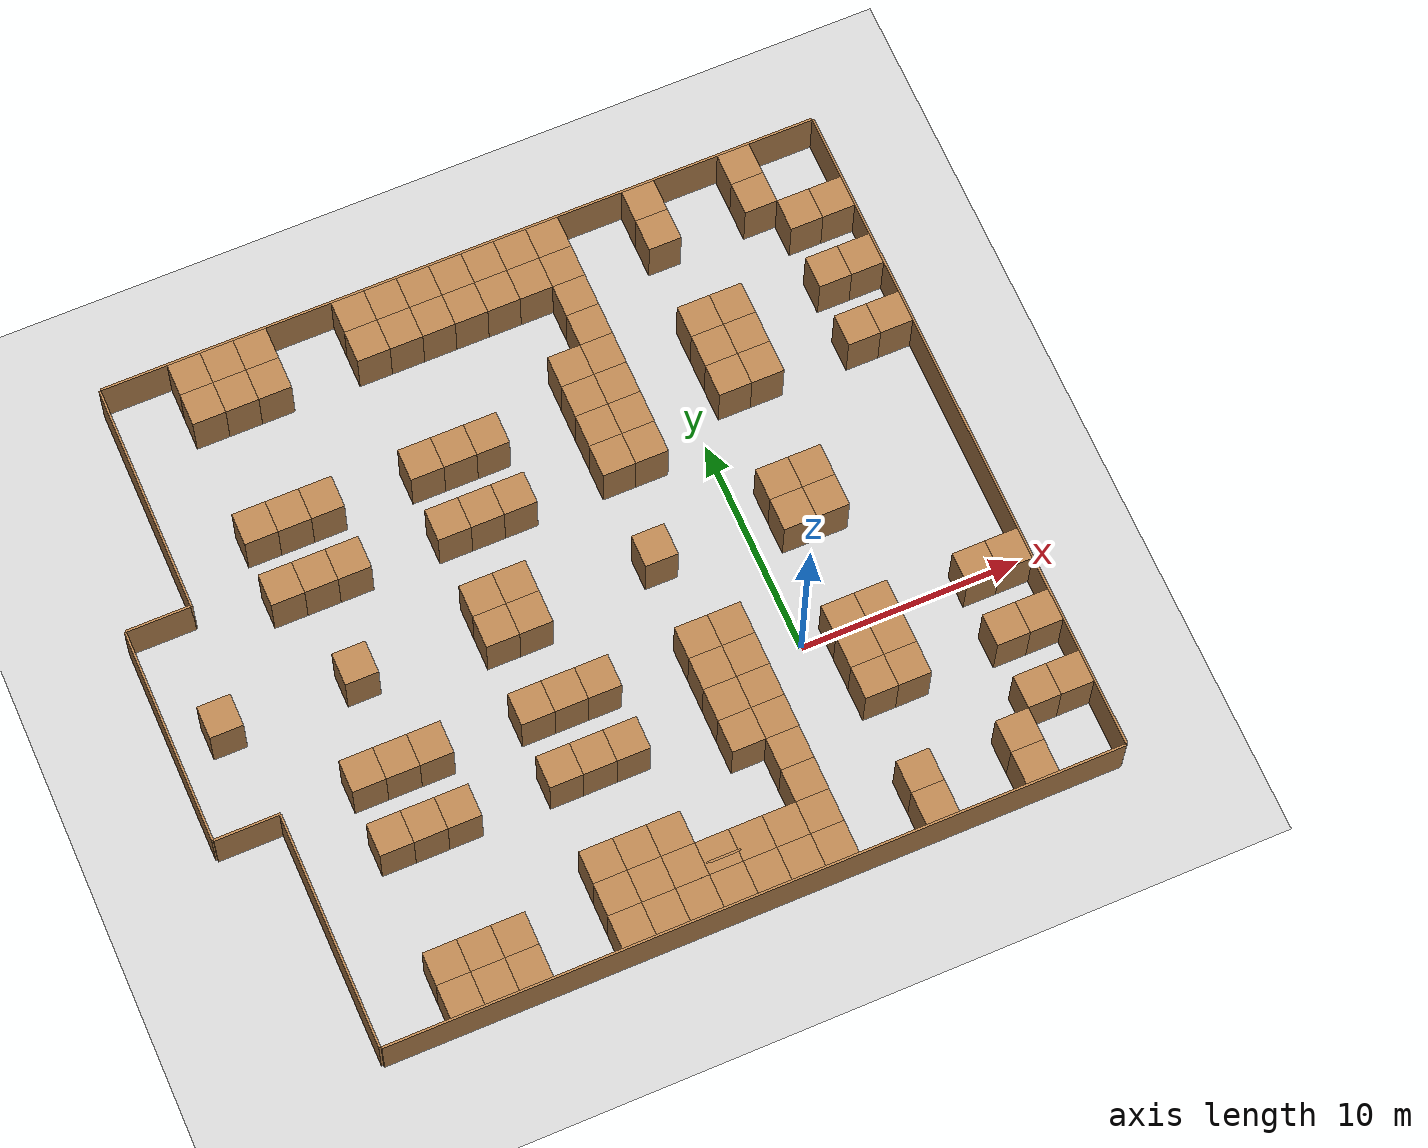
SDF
<sdf version="1.6">
 <world name="default">
  <light name="sun" type="directional">
   <pose>0 0 10 0 -0 0</pose>
   <diffuse>0.8 0.8 0.8 1</diffuse>
   <specular>0.1 0.1 0.1 1</specular>
   <attenuation>
    <range>1000</range>
    <constant>0.9</constant>
    <linear>0.01</linear>
    <quadratic>0.001</quadratic>
   </attenuation>
   <direction>-0.5 0.5 -1</direction>
  </light>
  <model name="ground_plane">
   <static>1</static>
   <link name="link">
    <collision name="collision">
     <geometry><plane><normal>0 0 1</normal><size>100 100</size></plane></geometry>
     <surface><friction><ode><mu>100</mu><mu2>50</mu2></ode></friction></surface>
    </collision>
    <visual name="visual">
     <cast_shadows>0</cast_shadows>
     <geometry><plane><normal>0 0 1</normal><size>100 100</size></plane></geometry>
     <material>
      <script><uri>file://media/materials/scripts/gazebo.material</uri><name>Gazebo/Grey</name></script>
     </material>
    </visual>
   </link>
  </model>
  <gravity>0 0 -9.8</gravity>
  <magnetic_field>6e-06 2.3e-05 -4.2e-05</magnetic_field>
  <atmosphere type="adiabatic"/>
  <physics name="default_physics" default="0" type="ode">
   <max_step_size>0.001</max_step_size>
   <real_time_factor>1</real_time_factor>
   <real_time_update_rate>1000</real_time_update_rate>
  </physics>
  <scene><ambient>0.4 0.4 0.4 1</ambient><background>0.7 0.7 0.7 1</background><shadows>1</shadows></scene>
  <spherical_coordinates>
   <surface_model>EARTH_WGS84</surface_model>
   <latitude_deg>0</latitude_deg>
   <longitude_deg>0</longitude_deg>
   <elevation>0</elevation>
   <heading_deg>0</heading_deg>
  </spherical_coordinates>
  <model name="wall_1.5_1.5_clone_clone">
   <pose>6.25 -7.75 0 0 -0 0</pose>
   <link name="Wall_2">
    <collision name="Wall_2_Collision">
     <geometry><box><size>1.5 1.5 2.5</size></box></geometry>
     <pose>0 0 1.25 0 -0 0</pose>
    </collision>
    <visual name="Wall_2_Visual">
     <pose>0 0 1.25 0 -0 0</pose>
     <geometry><box><size>1.5 1.5 2.5</size></box></geometry>
     <material>
      <script><uri>file://media/materials/scripts/gazebo.material</uri><name>Gazebo/Wood</name></script>
      <ambient>1 1 1 1</ambient>
     </material>
    </visual>
   </link>
   <static>1</static>
  </model>
  <model name="wall_1.5_1.5_clone_clone_0">
   <pose>6.25 -9.25 0 0 -0 0</pose>
   <link name="Wall_2">
    <collision name="Wall_2_Collision">
     <geometry><box><size>1.5 1.5 2.5</size></box></geometry>
     <pose>0 0 1.25 0 -0 0</pose>
    </collision>
    <visual name="Wall_2_Visual">
     <pose>0 0 1.25 0 -0 0</pose>
     <geometry><box><size>1.5 1.5 2.5</size></box></geometry>
     <material>
      <script><uri>file://media/materials/scripts/gazebo.material</uri><name>Gazebo/Wood</name></script>
      <ambient>1 1 1 1</ambient>
     </material>
    </visual>
   </link>
   <static>1</static>
  </model>
  <model name="wall_1.5_1.5_clone_clone_1">
   <pose>7.75 -6.25 0 0 -0 0</pose>
   <link name="Wall_2">
    <collision name="Wall_2_Collision">
     <geometry><box><size>1.5 1.5 2.5</size></box></geometry>
     <pose>0 0 1.25 0 -0 0</pose>
    </collision>
    <visual name="Wall_2_Visual">
     <pose>0 0 1.25 0 -0 0</pose>
     <geometry><box><size>1.5 1.5 2.5</size></box></geometry>
     <material>
      <script><uri>file://media/materials/scripts/gazebo.material</uri><name>Gazebo/Wood</name></script>
      <ambient>1 1 1 1</ambient>
     </material>
    </visual>
   </link>
   <static>1</static>
  </model>
  <model name="wall_1.5_1.5_clone_clone_2">
   <pose>9.25 -6.25 0 0 -0 0</pose>
   <link name="Wall_2">
    <collision name="Wall_2_Collision">
     <geometry><box><size>1.5 1.5 2.5</size></box></geometry>
     <pose>0 0 1.25 0 -0 0</pose>
    </collision>
    <visual name="Wall_2_Visual">
     <pose>0 0 1.25 0 -0 0</pose>
     <geometry><box><size>1.5 1.5 2.5</size></box></geometry>
     <material>
      <script><uri>file://media/materials/scripts/gazebo.material</uri><name>Gazebo/Wood</name></script>
      <ambient>1 1 1 1</ambient>
     </material>
    </visual>
   </link>
   <static>1</static>
  </model>
  <model name="wall_1.5_1.5_0">
   <pose>9.25 -3.25 0 0 -0 0</pose>
   <link name="Wall_2">
    <collision name="Wall_2_Collision">
     <geometry><box><size>1.5 1.5 2.5</size></box></geometry>
     <pose>0 0 1.25 0 -0 0</pose>
    </collision>
    <visual name="Wall_2_Visual">
     <pose>0 0 1.25 0 -0 0</pose>
     <geometry><box><size>1.5 1.5 2.5</size></box></geometry>
     <material>
      <script><uri>file://media/materials/scripts/gazebo.material</uri><name>Gazebo/Wood</name></script>
      <ambient>1 1 1 1</ambient>
     </material>
    </visual>
   </link>
   <static>1</static>
  </model>
  <model name="wall_1.5_1.5_0_clone">
   <pose>7.75 -3.25 0 0 -0 0</pose>
   <link name="Wall_2">
    <collision name="Wall_2_Collision">
     <geometry><box><size>1.5 1.5 2.5</size></box></geometry>
     <pose>0 0 1.25 0 -0 0</pose>
    </collision>
    <visual name="Wall_2_Visual">
     <pose>0 0 1.25 0 -0 0</pose>
     <geometry><box><size>1.5 1.5 2.5</size></box></geometry>
     <material>
      <script><uri>file://media/materials/scripts/gazebo.material</uri><name>Gazebo/Wood</name></script>
      <ambient>1 1 1 1</ambient>
     </material>
    </visual>
   </link>
   <static>1</static>
  </model>
  <model name="wall_1.5_1.5_1">
   <pose>9.25 -0.25 0 0 -0 0</pose>
   <link name="Wall_2">
    <collision name="Wall_2_Collision">
     <geometry><box><size>1.5 1.5 2.5</size></box></geometry>
     <pose>0 0 1.25 0 -0 0</pose>
    </collision>
    <visual name="Wall_2_Visual">
     <pose>0 0 1.25 0 -0 0</pose>
     <geometry><box><size>1.5 1.5 2.5</size></box></geometry>
     <material>
      <script><uri>file://media/materials/scripts/gazebo.material</uri><name>Gazebo/Wood</name></script>
      <ambient>1 1 1 1</ambient>
     </material>
    </visual>
   </link>
   <static>1</static>
  </model>
  <model name="wall_1.5_1.5_1_clone">
   <pose>7.75 -0.25 0 0 -0 0</pose>
   <link name="Wall_2">
    <collision name="Wall_2_Collision">
     <geometry><box><size>1.5 1.5 2.5</size></box></geometry>
     <pose>0 0 1.25 0 -0 0</pose>
    </collision>
    <visual name="Wall_2_Visual">
     <pose>0 0 1.25 0 -0 0</pose>
     <geometry><box><size>1.5 1.5 2.5</size></box></geometry>
     <material>
      <script><uri>file://media/materials/scripts/gazebo.material</uri><name>Gazebo/Wood</name></script>
      <ambient>1 1 1 1</ambient>
     </material>
    </visual>
   </link>
   <static>1</static>
  </model>
  <model name="wall_1.5_1.5_1_clone_clone">
   <pose>9.25 11.75 0 0 -0 0</pose>
   <link name="Wall_2">
    <collision name="Wall_2_Collision">
     <geometry><box><size>1.5 1.5 2.5</size></box></geometry>
     <pose>0 0 1.25 0 -0 0</pose>
    </collision>
    <visual name="Wall_2_Visual">
     <pose>0 0 1.25 0 -0 0</pose>
     <geometry><box><size>1.5 1.5 2.5</size></box></geometry>
     <material>
      <script><uri>file://media/materials/scripts/gazebo.material</uri><name>Gazebo/Wood</name></script>
      <ambient>1 1 1 1</ambient>
     </material>
    </visual>
   </link>
   <static>1</static>
  </model>
  <model name="wall_1.5_1.5_1_clone_clone_clone">
   <pose>7.75 11.75 0 0 -0 0</pose>
   <link name="Wall_2">
    <collision name="Wall_2_Collision">
     <geometry><box><size>1.5 1.5 2.5</size></box></geometry>
     <pose>0 0 1.25 0 -0 0</pose>
    </collision>
    <visual name="Wall_2_Visual">
     <pose>0 0 1.25 0 -0 0</pose>
     <geometry><box><size>1.5 1.5 2.5</size></box></geometry>
     <material>
      <script><uri>file://media/materials/scripts/gazebo.material</uri><name>Gazebo/Wood</name></script>
      <ambient>1 1 1 1</ambient>
     </material>
    </visual>
   </link>
   <static>1</static>
  </model>
  <model name="wall_1.5_1.5_1_clone_clone_clone_0">
   <pose>9.25 14.75 0 0 -0 0</pose>
   <link name="Wall_2">
    <collision name="Wall_2_Collision">
     <geometry><box><size>1.5 1.5 2.5</size></box></geometry>
     <pose>0 0 1.25 0 -0 0</pose>
    </collision>
    <visual name="Wall_2_Visual">
     <pose>0 0 1.25 0 -0 0</pose>
     <geometry><box><size>1.5 1.5 2.5</size></box></geometry>
     <material>
      <script><uri>file://media/materials/scripts/gazebo.material</uri><name>Gazebo/Wood</name></script>
      <ambient>1 1 1 1</ambient>
     </material>
    </visual>
   </link>
   <static>1</static>
  </model>
  <model name="wall_1.5_1.5_1_clone_clone_clone_1">
   <pose>7.75 14.75 0 0 -0 0</pose>
   <link name="Wall_2">
    <collision name="Wall_2_Collision">
     <geometry><box><size>1.5 1.5 2.5</size></box></geometry>
     <pose>0 0 1.25 0 -0 0</pose>
    </collision>
    <visual name="Wall_2_Visual">
     <pose>0 0 1.25 0 -0 0</pose>
     <geometry><box><size>1.5 1.5 2.5</size></box></geometry>
     <material>
      <script><uri>file://media/materials/scripts/gazebo.material</uri><name>Gazebo/Wood</name></script>
      <ambient>1 1 1 1</ambient>
     </material>
    </visual>
   </link>
   <static>1</static>
  </model>
  <model name="wall_1.5_1.5_1_clone_clone_clone_0_clone">
   <pose>9.25 17.75 0 0 -0 0</pose>
   <link name="Wall_2">
    <collision name="Wall_2_Collision">
     <geometry><box><size>1.5 1.5 2.5</size></box></geometry>
     <pose>0 0 1.25 0 -0 0</pose>
    </collision>
    <visual name="Wall_2_Visual">
     <pose>0 0 1.25 0 -0 0</pose>
     <geometry><box><size>1.5 1.5 2.5</size></box></geometry>
     <material>
      <script><uri>file://media/materials/scripts/gazebo.material</uri><name>Gazebo/Wood</name></script>
      <ambient>1 1 1 1</ambient>
     </material>
    </visual>
   </link>
   <static>1</static>
  </model>
  <model name="wall_1.5_1.5_1_clone_clone_clone_0_clone_0">
   <pose>7.75 17.75 0 0 -0 0</pose>
   <link name="Wall_2">
    <collision name="Wall_2_Collision">
     <geometry><box><size>1.5 1.5 2.5</size></box></geometry>
     <pose>0 0 1.25 0 -0 0</pose>
    </collision>
    <visual name="Wall_2_Visual">
     <pose>0 0 1.25 0 -0 0</pose>
     <geometry><box><size>1.5 1.5 2.5</size></box></geometry>
     <material>
      <script><uri>file://media/materials/scripts/gazebo.material</uri><name>Gazebo/Wood</name></script>
      <ambient>1 1 1 1</ambient>
     </material>
    </visual>
   </link>
   <static>1</static>
  </model>
  <model name="wall_1.5_1.5_1_clone_clone_clone_0_clone_0_clone">
   <pose>6.25 19.25 0 0 -0 0</pose>
   <link name="Wall_2">
    <collision name="Wall_2_Collision">
     <geometry><box><size>1.5 1.5 2.5</size></box></geometry>
     <pose>0 0 1.25 0 -0 0</pose>
    </collision>
    <visual name="Wall_2_Visual">
     <pose>0 0 1.25 0 -0 0</pose>
     <geometry><box><size>1.5 1.5 2.5</size></box></geometry>
     <material>
      <script><uri>file://media/materials/scripts/gazebo.material</uri><name>Gazebo/Wood</name></script>
      <ambient>1 1 1 1</ambient>
     </material>
    </visual>
   </link>
   <static>1</static>
  </model>
  <model name="wall_1.5_1.5_1_clone_clone_clone_0_clone_0_clone_0">
   <pose>6.25 20.75 0 0 -0 0</pose>
   <link name="Wall_2">
    <collision name="Wall_2_Collision">
     <geometry><box><size>1.5 1.5 2.5</size></box></geometry>
     <pose>0 0 1.25 0 -0 0</pose>
    </collision>
    <visual name="Wall_2_Visual">
     <pose>0 0 1.25 0 -0 0</pose>
     <geometry><box><size>1.5 1.5 2.5</size></box></geometry>
     <material>
      <script><uri>file://media/materials/scripts/gazebo.material</uri><name>Gazebo/Wood</name></script>
      <ambient>1 1 1 1</ambient>
     </material>
    </visual>
   </link>
   <static>1</static>
  </model>
  <model name="wall_1.5_1.5_clone_clone_clone">
   <pose>3.25 -3.25 0 0 -0 0</pose>
   <link name="Wall_2">
    <collision name="Wall_2_Collision">
     <geometry><box><size>1.5 1.5 2.5</size></box></geometry>
     <pose>0 0 1.25 0 -0 0</pose>
    </collision>
    <visual name="Wall_2_Visual">
     <pose>0 0 1.25 0 -0 0</pose>
     <geometry><box><size>1.5 1.5 2.5</size></box></geometry>
     <material>
      <script><uri>file://media/materials/scripts/gazebo.material</uri><name>Gazebo/Wood</name></script>
      <ambient>1 1 1 1</ambient>
     </material>
    </visual>
   </link>
   <static>1</static>
  </model>
  <model name="wall_1.5_1.5_clone_clone_clone_clone">
   <pose>3.25 -1.75 0 0 -0 0</pose>
   <link name="Wall_2">
    <collision name="Wall_2_Collision">
     <geometry><box><size>1.5 1.5 2.5</size></box></geometry>
     <pose>0 0 1.25 0 -0 0</pose>
    </collision>
    <visual name="Wall_2_Visual">
     <pose>0 0 1.25 0 -0 0</pose>
     <geometry><box><size>1.5 1.5 2.5</size></box></geometry>
     <material>
      <script><uri>file://media/materials/scripts/gazebo.material</uri><name>Gazebo/Wood</name></script>
      <ambient>1 1 1 1</ambient>
     </material>
    </visual>
   </link>
   <static>1</static>
  </model>
  <model name="wall_1.5_1.5_clone_clone_clone_clone_clone">
   <pose>1.75 -0.25 0 0 -0 0</pose>
   <link name="Wall_2">
    <collision name="Wall_2_Collision">
     <geometry><box><size>1.5 1.5 2.5</size></box></geometry>
     <pose>0 0 1.25 0 -0 0</pose>
    </collision>
    <visual name="Wall_2_Visual">
     <pose>0 0 1.25 0 -0 0</pose>
     <geometry><box><size>1.5 1.5 2.5</size></box></geometry>
     <material>
      <script><uri>file://media/materials/scripts/gazebo.material</uri><name>Gazebo/Wood</name></script>
      <ambient>1 1 1 1</ambient>
     </material>
    </visual>
   </link>
   <static>1</static>
  </model>
  <model name="wall_1.5_1.5_clone_clone_clone_clone_0">
   <pose>1.75 -3.25 0 0 -0 0</pose>
   <link name="Wall_2">
    <collision name="Wall_2_Collision">
     <geometry><box><size>1.5 1.5 2.5</size></box></geometry>
     <pose>0 0 1.25 0 -0 0</pose>
    </collision>
    <visual name="Wall_2_Visual">
     <pose>0 0 1.25 0 -0 0</pose>
     <geometry><box><size>1.5 1.5 2.5</size></box></geometry>
     <material>
      <script><uri>file://media/materials/scripts/gazebo.material</uri><name>Gazebo/Wood</name></script>
      <ambient>1 1 1 1</ambient>
     </material>
    </visual>
   </link>
   <static>1</static>
  </model>
  <model name="wall_1.5_1.5_clone_clone_clone_clone_0_clone">
   <pose>1.75 -1.75 0 0 -0 0</pose>
   <link name="Wall_2">
    <collision name="Wall_2_Collision">
     <geometry><box><size>1.5 1.5 2.5</size></box></geometry>
     <pose>0 0 1.25 0 -0 0</pose>
    </collision>
    <visual name="Wall_2_Visual">
     <pose>0 0 1.25 0 -0 0</pose>
     <geometry><box><size>1.5 1.5 2.5</size></box></geometry>
     <material>
      <script><uri>file://media/materials/scripts/gazebo.material</uri><name>Gazebo/Wood</name></script>
      <ambient>1 1 1 1</ambient>
     </material>
    </visual>
   </link>
   <static>1</static>
  </model>
  <model name="wall_1.5_1.5_clone_clone_clone_clone_clone_clone">
   <pose>3.25 -0.25 0 0 -0 0</pose>
   <link name="Wall_2">
    <collision name="Wall_2_Collision">
     <geometry><box><size>1.5 1.5 2.5</size></box></geometry>
     <pose>0 0 1.25 0 -0 0</pose>
    </collision>
    <visual name="Wall_2_Visual">
     <pose>0 0 1.25 0 -0 0</pose>
     <geometry><box><size>1.5 1.5 2.5</size></box></geometry>
     <material>
      <script><uri>file://media/materials/scripts/gazebo.material</uri><name>Gazebo/Wood</name></script>
      <ambient>1 1 1 1</ambient>
     </material>
    </visual>
   </link>
   <static>1</static>
  </model>
  <model name="wall_1.5_1.5_clone_clone_clone_clone_clone_clone_clone">
   <pose>3.25 6.5 0 0 -0 0</pose>
   <link name="Wall_2">
    <collision name="Wall_2_Collision">
     <geometry><box><size>1.5 1.5 2.5</size></box></geometry>
     <pose>0 0 1.25 0 -0 0</pose>
    </collision>
    <visual name="Wall_2_Visual">
     <pose>0 0 1.25 0 -0 0</pose>
     <geometry><box><size>1.5 1.5 2.5</size></box></geometry>
     <material>
      <script><uri>file://media/materials/scripts/gazebo.material</uri><name>Gazebo/Wood</name></script>
      <ambient>1 1 1 1</ambient>
     </material>
    </visual>
   </link>
   <static>1</static>
  </model>
  <model name="wall_1.5_1.5_clone_clone_clone_clone_clone_clone_clone_clone">
   <pose>3.25 5 0 0 -0 0</pose>
   <link name="Wall_2">
    <collision name="Wall_2_Collision">
     <geometry><box><size>1.5 1.5 2.5</size></box></geometry>
     <pose>0 0 1.25 0 -0 0</pose>
    </collision>
    <visual name="Wall_2_Visual">
     <pose>0 0 1.25 0 -0 0</pose>
     <geometry><box><size>1.5 1.5 2.5</size></box></geometry>
     <material>
      <script><uri>file://media/materials/scripts/gazebo.material</uri><name>Gazebo/Wood</name></script>
      <ambient>1 1 1 1</ambient>
     </material>
    </visual>
   </link>
   <static>1</static>
  </model>
  <model name="wall_1.5_1.5_clone_clone_clone_clone_clone_clone_clone_clone_0">
   <pose>1.75 6.5 0 0 -0 0</pose>
   <link name="Wall_2">
    <collision name="Wall_2_Collision">
     <geometry><box><size>1.5 1.5 2.5</size></box></geometry>
     <pose>0 0 1.25 0 -0 0</pose>
    </collision>
    <visual name="Wall_2_Visual">
     <pose>0 0 1.25 0 -0 0</pose>
     <geometry><box><size>1.5 1.5 2.5</size></box></geometry>
     <material>
      <script><uri>file://media/materials/scripts/gazebo.material</uri><name>Gazebo/Wood</name></script>
      <ambient>1 1 1 1</ambient>
     </material>
    </visual>
   </link>
   <static>1</static>
  </model>
  <model name="wall_1.5_1.5_clone_clone_clone_clone_clone_clone_clone_clone_1">
   <pose>1.75 5 0 0 -0 0</pose>
   <link name="Wall_2">
    <collision name="Wall_2_Collision">
     <geometry><box><size>1.5 1.5 2.5</size></box></geometry>
     <pose>0 0 1.25 0 -0 0</pose>
    </collision>
    <visual name="Wall_2_Visual">
     <pose>0 0 1.25 0 -0 0</pose>
     <geometry><box><size>1.5 1.5 2.5</size></box></geometry>
     <material>
      <script><uri>file://media/materials/scripts/gazebo.material</uri><name>Gazebo/Wood</name></script>
      <ambient>1 1 1 1</ambient>
     </material>
    </visual>
   </link>
   <static>1</static>
  </model>
  <model name="wall_1.5_1.5_clone_clone_clone_clone_clone_clone_clone_clone_clone_1">
   <pose>1.75 20.75 0 0 -0 0</pose>
   <link name="Wall_2">
    <collision name="Wall_2_Collision">
     <geometry><box><size>1.5 1.5 2.5</size></box></geometry>
     <pose>0 0 1.25 0 -0 0</pose>
    </collision>
    <visual name="Wall_2_Visual">
     <pose>0 0 1.25 0 -0 0</pose>
     <geometry><box><size>1.5 1.5 2.5</size></box></geometry>
     <material>
      <script><uri>file://media/materials/scripts/gazebo.material</uri><name>Gazebo/Wood</name></script>
      <ambient>1 1 1 1</ambient>
     </material>
    </visual>
   </link>
   <static>1</static>
  </model>
  <model name="wall_1.5_1.5_4">
   <pose>1.75 -9.25 0 0 -0 0</pose>
   <link name="Wall_2">
    <collision name="Wall_2_Collision">
     <geometry><box><size>1.5 1.5 2.5</size></box></geometry>
     <pose>0 0 1.25 0 -0 0</pose>
    </collision>
    <visual name="Wall_2_Visual">
     <pose>0 0 1.25 0 -0 0</pose>
     <geometry><box><size>1.5 1.5 2.5</size></box></geometry>
     <material>
      <script><uri>file://media/materials/scripts/gazebo.material</uri><name>Gazebo/Wood</name></script>
      <ambient>1 1 1 1</ambient>
     </material>
    </visual>
   </link>
   <static>1</static>
  </model>
  <model name="wall_1.5_1.5_4_clone">
   <pose>-2.75 -9.25 0 0 -0 0</pose>
   <link name="Wall_2">
    <collision name="Wall_2_Collision">
     <geometry><box><size>1.5 1.5 2.5</size></box></geometry>
     <pose>0 0 1.25 0 -0 0</pose>
    </collision>
    <visual name="Wall_2_Visual">
     <pose>0 0 1.25 0 -0 0</pose>
     <geometry><box><size>1.5 1.5 2.5</size></box></geometry>
     <material>
      <script><uri>file://media/materials/scripts/gazebo.material</uri><name>Gazebo/Wood</name></script>
      <ambient>1 1 1 1</ambient>
     </material>
    </visual>
   </link>
   <static>1</static>
  </model>
  <model name="wall_1.5_1.5_4_clone_clone">
   <pose>-2.75 -7.75 0 0 -0 0</pose>
   <link name="Wall_2">
    <collision name="Wall_2_Collision">
     <geometry><box><size>1.5 1.5 2.5</size></box></geometry>
     <pose>0 0 1.25 0 -0 0</pose>
    </collision>
    <visual name="Wall_2_Visual">
     <pose>0 0 1.25 0 -0 0</pose>
     <geometry><box><size>1.5 1.5 2.5</size></box></geometry>
     <material>
      <script><uri>file://media/materials/scripts/gazebo.material</uri><name>Gazebo/Wood</name></script>
      <ambient>1 1 1 1</ambient>
     </material>
    </visual>
   </link>
   <static>1</static>
  </model>
  <model name="wall_1.5_1.5_4_clone_clone_0">
   <pose>-2.75 -6.25 0 0 -0 0</pose>
   <link name="Wall_2">
    <collision name="Wall_2_Collision">
     <geometry><box><size>1.5 1.5 2.5</size></box></geometry>
     <pose>0 0 1.25 0 -0 0</pose>
    </collision>
    <visual name="Wall_2_Visual">
     <pose>0 0 1.25 0 -0 0</pose>
     <geometry><box><size>1.5 1.5 2.5</size></box></geometry>
     <material>
      <script><uri>file://media/materials/scripts/gazebo.material</uri><name>Gazebo/Wood</name></script>
      <ambient>1 1 1 1</ambient>
     </material>
    </visual>
   </link>
   <static>1</static>
  </model>
  <model name="wall_1.5_1.5_4_clone_clone_1">
   <pose>-2.75 -4.75 0 0 -0 0</pose>
   <link name="Wall_2">
    <collision name="Wall_2_Collision">
     <geometry><box><size>1.5 1.5 2.5</size></box></geometry>
     <pose>0 0 1.25 0 -0 0</pose>
    </collision>
    <visual name="Wall_2_Visual">
     <pose>0 0 1.25 0 -0 0</pose>
     <geometry><box><size>1.5 1.5 2.5</size></box></geometry>
     <material>
      <script><uri>file://media/materials/scripts/gazebo.material</uri><name>Gazebo/Wood</name></script>
      <ambient>1 1 1 1</ambient>
     </material>
    </visual>
   </link>
   <static>1</static>
  </model>
  <model name="wall_1.5_1.5_4_clone_clone_2">
   <pose>-2.75 -3.25 0 0 -0 0</pose>
   <link name="Wall_2">
    <collision name="Wall_2_Collision">
     <geometry><box><size>1.5 1.5 2.5</size></box></geometry>
     <pose>0 0 1.25 0 -0 0</pose>
    </collision>
    <visual name="Wall_2_Visual">
     <pose>0 0 1.25 0 -0 0</pose>
     <geometry><box><size>1.5 1.5 2.5</size></box></geometry>
     <material>
      <script><uri>file://media/materials/scripts/gazebo.material</uri><name>Gazebo/Wood</name></script>
      <ambient>1 1 1 1</ambient>
     </material>
    </visual>
   </link>
   <static>1</static>
  </model>
  <model name="wall_1.5_1.5_4_clone_clone_3">
   <pose>-2.75 -1.75 0 0 -0 0</pose>
   <link name="Wall_2">
    <collision name="Wall_2_Collision">
     <geometry><box><size>1.5 1.5 2.5</size></box></geometry>
     <pose>0 0 1.25 0 -0 0</pose>
    </collision>
    <visual name="Wall_2_Visual">
     <pose>0 0 1.25 0 -0 0</pose>
     <geometry><box><size>1.5 1.5 2.5</size></box></geometry>
     <material>
      <script><uri>file://media/materials/scripts/gazebo.material</uri><name>Gazebo/Wood</name></script>
      <ambient>1 1 1 1</ambient>
     </material>
    </visual>
   </link>
   <static>1</static>
  </model>
  <model name="wall_1.5_1.5_4_clone_clone_4">
   <pose>-2.75 -0.25 0 0 -0 0</pose>
   <link name="Wall_2">
    <collision name="Wall_2_Collision">
     <geometry><box><size>1.5 1.5 2.5</size></box></geometry>
     <pose>0 0 1.25 0 -0 0</pose>
    </collision>
    <visual name="Wall_2_Visual">
     <pose>0 0 1.25 0 -0 0</pose>
     <geometry><box><size>1.5 1.5 2.5</size></box></geometry>
     <material>
      <script><uri>file://media/materials/scripts/gazebo.material</uri><name>Gazebo/Wood</name></script>
      <ambient>1 1 1 1</ambient>
     </material>
    </visual>
   </link>
   <static>1</static>
  </model>
  <model name="wall_1.5_1.5_4_clone_clone_4_clone">
   <pose>-4.25 -0.25 0 0 -0 0</pose>
   <link name="Wall_2">
    <collision name="Wall_2_Collision">
     <geometry><box><size>1.5 1.5 2.5</size></box></geometry>
     <pose>0 0 1.25 0 -0 0</pose>
    </collision>
    <visual name="Wall_2_Visual">
     <pose>0 0 1.25 0 -0 0</pose>
     <geometry><box><size>1.5 1.5 2.5</size></box></geometry>
     <material>
      <script><uri>file://media/materials/scripts/gazebo.material</uri><name>Gazebo/Wood</name></script>
      <ambient>1 1 1 1</ambient>
     </material>
    </visual>
   </link>
   <static>1</static>
  </model>
  <model name="wall_1.5_1.5_4_clone_clone_4_clone_0">
   <pose>-4.25 -1.75 0 0 -0 0</pose>
   <link name="Wall_2">
    <collision name="Wall_2_Collision">
     <geometry><box><size>1.5 1.5 2.5</size></box></geometry>
     <pose>0 0 1.25 0 -0 0</pose>
    </collision>
    <visual name="Wall_2_Visual">
     <pose>0 0 1.25 0 -0 0</pose>
     <geometry><box><size>1.5 1.5 2.5</size></box></geometry>
     <material>
      <script><uri>file://media/materials/scripts/gazebo.material</uri><name>Gazebo/Wood</name></script>
      <ambient>1 1 1 1</ambient>
     </material>
    </visual>
   </link>
   <static>1</static>
  </model>
  <model name="wall_1.5_1.5_4_clone_clone_4_clone_1">
   <pose>-4.25 -3.25 0 0 -0 0</pose>
   <link name="Wall_2">
    <collision name="Wall_2_Collision">
     <geometry><box><size>1.5 1.5 2.5</size></box></geometry>
     <pose>0 0 1.25 0 -0 0</pose>
    </collision>
    <visual name="Wall_2_Visual">
     <pose>0 0 1.25 0 -0 0</pose>
     <geometry><box><size>1.5 1.5 2.5</size></box></geometry>
     <material>
      <script><uri>file://media/materials/scripts/gazebo.material</uri><name>Gazebo/Wood</name></script>
      <ambient>1 1 1 1</ambient>
     </material>
    </visual>
   </link>
   <static>1</static>
  </model>
  <model name="wall_1.5_1.5_4_clone_clone_4_clone_2">
   <pose>-4.25 -7.75 0 0 -0 0</pose>
   <link name="Wall_2">
    <collision name="Wall_2_Collision">
     <geometry><box><size>1.5 1.5 2.5</size></box></geometry>
     <pose>0 0 1.25 0 -0 0</pose>
    </collision>
    <visual name="Wall_2_Visual">
     <pose>0 0 1.25 0 -0 0</pose>
     <geometry><box><size>1.5 1.5 2.5</size></box></geometry>
     <material>
      <script><uri>file://media/materials/scripts/gazebo.material</uri><name>Gazebo/Wood</name></script>
      <ambient>1 1 1 1</ambient>
     </material>
    </visual>
   </link>
   <static>1</static>
  </model>
  <model name="wall_1.5_1.5_4_clone_clone_4_clone_3">
   <pose>-4.25 -9.25 0 0 -0 0</pose>
   <link name="Wall_2">
    <collision name="Wall_2_Collision">
     <geometry><box><size>1.5 1.5 2.5</size></box></geometry>
     <pose>0 0 1.25 0 -0 0</pose>
    </collision>
    <visual name="Wall_2_Visual">
     <pose>0 0 1.25 0 -0 0</pose>
     <geometry><box><size>1.5 1.5 2.5</size></box></geometry>
     <material>
      <script><uri>file://media/materials/scripts/gazebo.material</uri><name>Gazebo/Wood</name></script>
      <ambient>1 1 1 1</ambient>
     </material>
    </visual>
   </link>
   <static>1</static>
  </model>
  <model name="wall_1.5_1.5_5">
   <pose>-5.75 -9.25 0 0 -0 0</pose>
   <link name="Wall_2">
    <collision name="Wall_2_Collision">
     <geometry><box><size>1.5 1.5 2.5</size></box></geometry>
     <pose>0 0 1.25 0 -0 0</pose>
    </collision>
    <visual name="Wall_2_Visual">
     <pose>0 0 1.25 0 -0 0</pose>
     <geometry><box><size>1.5 1.5 2.5</size></box></geometry>
     <material>
      <script><uri>file://media/materials/scripts/gazebo.material</uri><name>Gazebo/Wood</name></script>
      <ambient>1 1 1 1</ambient>
     </material>
    </visual>
   </link>
   <static>1</static>
  </model>
  <model name="wall_1.5_1.5_4_clone_clone_4_clone_4">
   <pose>-5.75 -7.75 0 0 -0 0</pose>
   <link name="Wall_2">
    <collision name="Wall_2_Collision">
     <geometry><box><size>1.5 1.5 2.5</size></box></geometry>
     <pose>0 0 1.25 0 -0 0</pose>
    </collision>
    <visual name="Wall_2_Visual">
     <pose>0 0 1.25 0 -0 0</pose>
     <geometry><box><size>1.5 1.5 2.5</size></box></geometry>
     <material>
      <script><uri>file://media/materials/scripts/gazebo.material</uri><name>Gazebo/Wood</name></script>
      <ambient>1 1 1 1</ambient>
     </material>
    </visual>
   </link>
   <static>1</static>
  </model>
  <model name="wall_1.5_1.5_4_clone_clone_4_clone_5">
   <pose>-7.25 -9.25 0 0 -0 0</pose>
   <link name="Wall_2">
    <collision name="Wall_2_Collision">
     <geometry><box><size>1.5 1.5 2.5</size></box></geometry>
     <pose>0 0 1.25 0 -0 0</pose>
    </collision>
    <visual name="Wall_2_Visual">
     <pose>0 0 1.25 0 -0 0</pose>
     <geometry><box><size>1.5 1.5 2.5</size></box></geometry>
     <material>
      <script><uri>file://media/materials/scripts/gazebo.material</uri><name>Gazebo/Wood</name></script>
      <ambient>1 1 1 1</ambient>
     </material>
    </visual>
   </link>
   <static>1</static>
  </model>
  <model name="wall_1.5_1.5_4_clone_clone_4_clone_6">
   <pose>-7.25 -7.75 0 0 -0 0</pose>
   <link name="Wall_2">
    <collision name="Wall_2_Collision">
     <geometry><box><size>1.5 1.5 2.5</size></box></geometry>
     <pose>0 0 1.25 0 -0 0</pose>
    </collision>
    <visual name="Wall_2_Visual">
     <pose>0 0 1.25 0 -0 0</pose>
     <geometry><box><size>1.5 1.5 2.5</size></box></geometry>
     <material>
      <script><uri>file://media/materials/scripts/gazebo.material</uri><name>Gazebo/Wood</name></script>
      <ambient>1 1 1 1</ambient>
     </material>
    </visual>
   </link>
   <static>1</static>
  </model>
  <model name="wall_1.5_1.5_4_clone_clone_4_clone_7">
   <pose>-8.75 -9.25 0 0 -0 0</pose>
   <link name="Wall_2">
    <collision name="Wall_2_Collision">
     <geometry><box><size>1.5 1.5 2.5</size></box></geometry>
     <pose>0 0 1.25 0 -0 0</pose>
    </collision>
    <visual name="Wall_2_Visual">
     <pose>0 0 1.25 0 -0 0</pose>
     <geometry><box><size>1.5 1.5 2.5</size></box></geometry>
     <material>
      <script><uri>file://media/materials/scripts/gazebo.material</uri><name>Gazebo/Wood</name></script>
      <ambient>1 1 1 1</ambient>
     </material>
    </visual>
   </link>
   <static>1</static>
  </model>
  <model name="wall_1.5_1.5_4_clone_clone_4_clone_8">
   <pose>-8.75 -7.75 0.005554 0 -0 0</pose>
   <link name="Wall_2">
    <collision name="Wall_2_Collision">
     <geometry><box><size>1.5 1.5 2.5</size></box></geometry>
     <pose>0 0 1.25 0 -0 0</pose>
    </collision>
    <visual name="Wall_2_Visual">
     <pose>0 0 1.25 0 -0 0</pose>
     <geometry><box><size>1.5 1.5 2.5</size></box></geometry>
     <material>
      <script><uri>file://media/materials/scripts/gazebo.material</uri><name>Gazebo/Wood</name></script>
      <ambient>1 1 1 1</ambient>
     </material>
    </visual>
   </link>
   <static>1</static>
  </model>
  <model name="wall_1.5_1.5_4_clone_clone_4_clone_7_clone">
   <pose>-10.25 -9.25 0 0 -0 0</pose>
   <link name="Wall_2">
    <collision name="Wall_2_Collision">
     <geometry><box><size>1.5 1.5 2.5</size></box></geometry>
     <pose>0 0 1.25 0 -0 0</pose>
    </collision>
    <visual name="Wall_2_Visual">
     <pose>0 0 1.25 0 -0 0</pose>
     <geometry><box><size>1.5 1.5 2.5</size></box></geometry>
     <material>
      <script><uri>file://media/materials/scripts/gazebo.material</uri><name>Gazebo/Wood</name></script>
      <ambient>1 1 1 1</ambient>
     </material>
    </visual>
   </link>
   <static>1</static>
  </model>
  <model name="wall_1.5_1.5_4_clone_clone_4_clone_7_clone_0">
   <pose>-10.25 -7.75 0 0 -0 0</pose>
   <link name="Wall_2">
    <collision name="Wall_2_Collision">
     <geometry><box><size>1.5 1.5 2.5</size></box></geometry>
     <pose>0 0 1.25 0 -0 0</pose>
    </collision>
    <visual name="Wall_2_Visual">
     <pose>0 0 1.25 0 -0 0</pose>
     <geometry><box><size>1.5 1.5 2.5</size></box></geometry>
     <material>
      <script><uri>file://media/materials/scripts/gazebo.material</uri><name>Gazebo/Wood</name></script>
      <ambient>1 1 1 1</ambient>
     </material>
    </visual>
   </link>
   <static>1</static>
  </model>
  <model name="wall_1.5_1.5_4_clone_clone_4_clone_7_clone_1">
   <pose>-10.25 -6.25 0 0 -0 0</pose>
   <link name="Wall_2">
    <collision name="Wall_2_Collision">
     <geometry><box><size>1.5 1.5 2.5</size></box></geometry>
     <pose>0 0 1.25 0 -0 0</pose>
    </collision>
    <visual name="Wall_2_Visual">
     <pose>0 0 1.25 0 -0 0</pose>
     <geometry><box><size>1.5 1.5 2.5</size></box></geometry>
     <material>
      <script><uri>file://media/materials/scripts/gazebo.material</uri><name>Gazebo/Wood</name></script>
      <ambient>1 1 1 1</ambient>
     </material>
    </visual>
   </link>
   <static>1</static>
  </model>
  <model name="wall_1.5_1.5_4_clone_clone_4_clone_7_clone_2">
   <pose>-8.75 -6.25 0 0 -0 0</pose>
   <link name="Wall_2">
    <collision name="Wall_2_Collision">
     <geometry><box><size>1.5 1.5 2.5</size></box></geometry>
     <pose>0 0 1.25 0 -0 0</pose>
    </collision>
    <visual name="Wall_2_Visual">
     <pose>0 0 1.25 0 -0 0</pose>
     <geometry><box><size>1.5 1.5 2.5</size></box></geometry>
     <material>
      <script><uri>file://media/materials/scripts/gazebo.material</uri><name>Gazebo/Wood</name></script>
      <ambient>1 1 1 1</ambient>
     </material>
    </visual>
   </link>
   <static>1</static>
  </model>
  <model name="wall_1.5_1.5_6">
   <pose>-11.75 -9.25 0 0 -0 0</pose>
   <link name="Wall_2">
    <collision name="Wall_2_Collision">
     <geometry><box><size>1.5 1.5 2.5</size></box></geometry>
     <pose>0 0 1.25 0 -0 0</pose>
    </collision>
    <visual name="Wall_2_Visual">
     <pose>0 0 1.25 0 -0 0</pose>
     <geometry><box><size>1.5 1.5 2.5</size></box></geometry>
     <material>
      <script><uri>file://media/materials/scripts/gazebo.material</uri><name>Gazebo/Wood</name></script>
      <ambient>1 1 1 1</ambient>
     </material>
    </visual>
   </link>
   <static>1</static>
  </model>
  <model name="wall_1.5_1.5_4_clone_clone_4_clone_7_clone_4">
   <pose>-11.75 -7.75 0 0 -0 0</pose>
   <link name="Wall_2">
    <collision name="Wall_2_Collision">
     <geometry><box><size>1.5 1.5 2.5</size></box></geometry>
     <pose>0 0 1.25 0 -0 0</pose>
    </collision>
    <visual name="Wall_2_Visual">
     <pose>0 0 1.25 0 -0 0</pose>
     <geometry><box><size>1.5 1.5 2.5</size></box></geometry>
     <material>
      <script><uri>file://media/materials/scripts/gazebo.material</uri><name>Gazebo/Wood</name></script>
      <ambient>1 1 1 1</ambient>
     </material>
    </visual>
   </link>
   <static>1</static>
  </model>
  <model name="wall_1.5_1.5_4_clone_clone_4_clone_7_clone_5">
   <pose>-11.75 -6.25 0 0 -0 0</pose>
   <link name="Wall_2">
    <collision name="Wall_2_Collision">
     <geometry><box><size>1.5 1.5 2.5</size></box></geometry>
     <pose>0 0 1.25 0 -0 0</pose>
    </collision>
    <visual name="Wall_2_Visual">
     <pose>0 0 1.25 0 -0 0</pose>
     <geometry><box><size>1.5 1.5 2.5</size></box></geometry>
     <material>
      <script><uri>file://media/materials/scripts/gazebo.material</uri><name>Gazebo/Wood</name></script>
      <ambient>1 1 1 1</ambient>
     </material>
    </visual>
   </link>
   <static>1</static>
  </model>
  <model name="wall_1.5_1.5_7">
   <pose>-8.75 -1.75 0 0 -0 0</pose>
   <link name="Wall_2">
    <collision name="Wall_2_Collision">
     <geometry><box><size>1.5 1.5 2.5</size></box></geometry>
     <pose>0 0 1.25 0 -0 0</pose>
    </collision>
    <visual name="Wall_2_Visual">
     <pose>0 0 1.25 0 -0 0</pose>
     <geometry><box><size>1.5 1.5 2.5</size></box></geometry>
     <material>
      <script><uri>file://media/materials/scripts/gazebo.material</uri><name>Gazebo/Wood</name></script>
      <ambient>1 1 1 1</ambient>
     </material>
    </visual>
   </link>
   <static>1</static>
  </model>
  <model name="wall_1.5_1.5_4_clone_clone_4_clone_7_clone_3">
   <pose>-10.25 -1.75 0 0 -0 0</pose>
   <link name="Wall_2">
    <collision name="Wall_2_Collision">
     <geometry><box><size>1.5 1.5 2.5</size></box></geometry>
     <pose>0 0 1.25 0 -0 0</pose>
    </collision>
    <visual name="Wall_2_Visual">
     <pose>0 0 1.25 0 -0 0</pose>
     <geometry><box><size>1.5 1.5 2.5</size></box></geometry>
     <material>
      <script><uri>file://media/materials/scripts/gazebo.material</uri><name>Gazebo/Wood</name></script>
      <ambient>1 1 1 1</ambient>
     </material>
    </visual>
   </link>
   <static>1</static>
  </model>
  <model name="wall_1.5_1.5_4_clone_clone_4_clone_7_clone_6">
   <pose>-11.75 -1.75 0 0 -0 0</pose>
   <link name="Wall_2">
    <collision name="Wall_2_Collision">
     <geometry><box><size>1.5 1.5 2.5</size></box></geometry>
     <pose>0 0 1.25 0 -0 0</pose>
    </collision>
    <visual name="Wall_2_Visual">
     <pose>0 0 1.25 0 -0 0</pose>
     <geometry><box><size>1.5 1.5 2.5</size></box></geometry>
     <material>
      <script><uri>file://media/materials/scripts/gazebo.material</uri><name>Gazebo/Wood</name></script>
      <ambient>1 1 1 1</ambient>
     </material>
    </visual>
   </link>
   <static>1</static>
  </model>
  <model name="wall_1.5_1.5_4_clone_clone_4_clone_7_clone_9">
   <pose>-16.25 -9.25 0 0 -0 0</pose>
   <link name="Wall_2">
    <collision name="Wall_2_Collision">
     <geometry><box><size>1.5 1.5 2.5</size></box></geometry>
     <pose>0 0 1.25 0 -0 0</pose>
    </collision>
    <visual name="Wall_2_Visual">
     <pose>0 0 1.25 0 -0 0</pose>
     <geometry><box><size>1.5 1.5 2.5</size></box></geometry>
     <material>
      <script><uri>file://media/materials/scripts/gazebo.material</uri><name>Gazebo/Wood</name></script>
      <ambient>1 1 1 1</ambient>
     </material>
    </visual>
   </link>
   <static>1</static>
  </model>
  <model name="wall_1.5_1.5_4_clone_clone_4_clone_7_clone_9_clone">
   <pose>-17.75 -9.25 0 0 -0 0</pose>
   <link name="Wall_2">
    <collision name="Wall_2_Collision">
     <geometry><box><size>1.5 1.5 2.5</size></box></geometry>
     <pose>0 0 1.25 0 -0 0</pose>
    </collision>
    <visual name="Wall_2_Visual">
     <pose>0 0 1.25 0 -0 0</pose>
     <geometry><box><size>1.5 1.5 2.5</size></box></geometry>
     <material>
      <script><uri>file://media/materials/scripts/gazebo.material</uri><name>Gazebo/Wood</name></script>
      <ambient>1 1 1 1</ambient>
     </material>
    </visual>
   </link>
   <static>1</static>
  </model>
  <model name="wall_1.5_1.5_4_clone_clone_4_clone_7_clone_9_clone_0">
   <pose>-19.25 -9.25 0 0 -0 0</pose>
   <link name="Wall_2">
    <collision name="Wall_2_Collision">
     <geometry><box><size>1.5 1.5 2.5</size></box></geometry>
     <pose>0 0 1.25 0 -0 0</pose>
    </collision>
    <visual name="Wall_2_Visual">
     <pose>0 0 1.25 0 -0 0</pose>
     <geometry><box><size>1.5 1.5 2.5</size></box></geometry>
     <material>
      <script><uri>file://media/materials/scripts/gazebo.material</uri><name>Gazebo/Wood</name></script>
      <ambient>1 1 1 1</ambient>
     </material>
    </visual>
   </link>
   <static>1</static>
  </model>
  <model name="wall_1.5_1.5_4_clone_clone_4_clone_7_clone_9_clone_1">
   <pose>-19.25 -7.75 0 0 -0 0</pose>
   <link name="Wall_2">
    <collision name="Wall_2_Collision">
     <geometry><box><size>1.5 1.5 2.5</size></box></geometry>
     <pose>0 0 1.25 0 -0 0</pose>
    </collision>
    <visual name="Wall_2_Visual">
     <pose>0 0 1.25 0 -0 0</pose>
     <geometry><box><size>1.5 1.5 2.5</size></box></geometry>
     <material>
      <script><uri>file://media/materials/scripts/gazebo.material</uri><name>Gazebo/Wood</name></script>
      <ambient>1 1 1 1</ambient>
     </material>
    </visual>
   </link>
   <static>1</static>
  </model>
  <model name="wall_1.5_1.5_4_clone_clone_4_clone_7_clone_9_clone_2">
   <pose>-17.75 -7.75 0 0 -0 0</pose>
   <link name="Wall_2">
    <collision name="Wall_2_Collision">
     <geometry><box><size>1.5 1.5 2.5</size></box></geometry>
     <pose>0 0 1.25 0 -0 0</pose>
    </collision>
    <visual name="Wall_2_Visual">
     <pose>0 0 1.25 0 -0 0</pose>
     <geometry><box><size>1.5 1.5 2.5</size></box></geometry>
     <material>
      <script><uri>file://media/materials/scripts/gazebo.material</uri><name>Gazebo/Wood</name></script>
      <ambient>1 1 1 1</ambient>
     </material>
    </visual>
   </link>
   <static>1</static>
  </model>
  <model name="wall_1.5_1.5_4_clone_clone_4_clone_7_clone_9_clone_3">
   <pose>-16.25 -7.75 0 0 -0 0</pose>
   <link name="Wall_2">
    <collision name="Wall_2_Collision">
     <geometry><box><size>1.5 1.5 2.5</size></box></geometry>
     <pose>0 0 1.25 0 -0 0</pose>
    </collision>
    <visual name="Wall_2_Visual">
     <pose>0 0 1.25 0 -0 0</pose>
     <geometry><box><size>1.5 1.5 2.5</size></box></geometry>
     <material>
      <script><uri>file://media/materials/scripts/gazebo.material</uri><name>Gazebo/Wood</name></script>
      <ambient>1 1 1 1</ambient>
     </material>
    </visual>
   </link>
   <static>1</static>
  </model>
  <model name="wall_1.5_1.5_4_clone_clone_4_clone_9">
   <pose>-2.75 1.25 0 0 -0 0</pose>
   <link name="Wall_2">
    <collision name="Wall_2_Collision">
     <geometry><box><size>1.5 1.5 2.5</size></box></geometry>
     <pose>0 0 1.25 0 -0 0</pose>
    </collision>
    <visual name="Wall_2_Visual">
     <pose>0 0 1.25 0 -0 0</pose>
     <geometry><box><size>1.5 1.5 2.5</size></box></geometry>
     <material>
      <script><uri>file://media/materials/scripts/gazebo.material</uri><name>Gazebo/Wood</name></script>
      <ambient>1 1 1 1</ambient>
     </material>
    </visual>
   </link>
   <static>1</static>
  </model>
  <model name="wall_1.5_1.5_4_clone_clone_4_clone_10">
   <pose>-4.25 1.25 0 0 -0 0</pose>
   <link name="Wall_2">
    <collision name="Wall_2_Collision">
     <geometry><box><size>1.5 1.5 2.5</size></box></geometry>
     <pose>0 0 1.25 0 -0 0</pose>
    </collision>
    <visual name="Wall_2_Visual">
     <pose>0 0 1.25 0 -0 0</pose>
     <geometry><box><size>1.5 1.5 2.5</size></box></geometry>
     <material>
      <script><uri>file://media/materials/scripts/gazebo.material</uri><name>Gazebo/Wood</name></script>
      <ambient>1 1 1 1</ambient>
     </material>
    </visual>
   </link>
   <static>1</static>
  </model>
  <model name="wall_1.5_1.5_4_clone_clone_4_clone_13">
   <pose>-8.75 1.25 0 0 -0 0</pose>
   <link name="Wall_2">
    <collision name="Wall_2_Collision">
     <geometry><box><size>1.5 1.5 2.5</size></box></geometry>
     <pose>0 0 1.25 0 -0 0</pose>
    </collision>
    <visual name="Wall_2_Visual">
     <pose>0 0 1.25 0 -0 0</pose>
     <geometry><box><size>1.5 1.5 2.5</size></box></geometry>
     <material>
      <script><uri>file://media/materials/scripts/gazebo.material</uri><name>Gazebo/Wood</name></script>
      <ambient>1 1 1 1</ambient>
     </material>
    </visual>
   </link>
   <static>1</static>
  </model>
  <model name="wall_1.5_1.5_4_clone_clone_4_clone_13_clone">
   <pose>-10.25 1.25 0 0 -0 0</pose>
   <link name="Wall_2">
    <collision name="Wall_2_Collision">
     <geometry><box><size>1.5 1.5 2.5</size></box></geometry>
     <pose>0 0 1.25 0 -0 0</pose>
    </collision>
    <visual name="Wall_2_Visual">
     <pose>0 0 1.25 0 -0 0</pose>
     <geometry><box><size>1.5 1.5 2.5</size></box></geometry>
     <material>
      <script><uri>file://media/materials/scripts/gazebo.material</uri><name>Gazebo/Wood</name></script>
      <ambient>1 1 1 1</ambient>
     </material>
    </visual>
   </link>
   <static>1</static>
  </model>
  <model name="wall_1.5_1.5_4_clone_clone_4_clone_13_clone_0">
   <pose>-11.75 1.25 0 0 -0 0</pose>
   <link name="Wall_2">
    <collision name="Wall_2_Collision">
     <geometry><box><size>1.5 1.5 2.5</size></box></geometry>
     <pose>0 0 1.25 0 -0 0</pose>
    </collision>
    <visual name="Wall_2_Visual">
     <pose>0 0 1.25 0 -0 0</pose>
     <geometry><box><size>1.5 1.5 2.5</size></box></geometry>
     <material>
      <script><uri>file://media/materials/scripts/gazebo.material</uri><name>Gazebo/Wood</name></script>
      <ambient>1 1 1 1</ambient>
     </material>
    </visual>
   </link>
   <static>1</static>
  </model>
  <model name="wall_1.5_1.5_4_clone_clone_4_clone_7_clone_9_clone_1_clone">
   <pose>-16.25 -1.75 0 0 -0 0</pose>
   <link name="Wall_2">
    <collision name="Wall_2_Collision">
     <geometry><box><size>1.5 1.5 2.5</size></box></geometry>
     <pose>0 0 1.25 0 -0 0</pose>
    </collision>
    <visual name="Wall_2_Visual">
     <pose>0 0 1.25 0 -0 0</pose>
     <geometry><box><size>1.5 1.5 2.5</size></box></geometry>
     <material>
      <script><uri>file://media/materials/scripts/gazebo.material</uri><name>Gazebo/Wood</name></script>
      <ambient>1 1 1 1</ambient>
     </material>
    </visual>
   </link>
   <static>1</static>
  </model>
  <model name="wall_1.5_1.5_4_clone_clone_4_clone_7_clone_9_clone_1_clone_clone">
   <pose>-17.75 -1.75 0 0 -0 0</pose>
   <link name="Wall_2">
    <collision name="Wall_2_Collision">
     <geometry><box><size>1.5 1.5 2.5</size></box></geometry>
     <pose>0 0 1.25 0 -0 0</pose>
    </collision>
    <visual name="Wall_2_Visual">
     <pose>0 0 1.25 0 -0 0</pose>
     <geometry><box><size>1.5 1.5 2.5</size></box></geometry>
     <material>
      <script><uri>file://media/materials/scripts/gazebo.material</uri><name>Gazebo/Wood</name></script>
      <ambient>1 1 1 1</ambient>
     </material>
    </visual>
   </link>
   <static>1</static>
  </model>
  <model name="wall_1.5_1.5_4_clone_clone_4_clone_7_clone_9_clone_1_clone_clone_0">
   <pose>-19.25 -1.75 0 0 -0 0</pose>
   <link name="Wall_2">
    <collision name="Wall_2_Collision">
     <geometry><box><size>1.5 1.5 2.5</size></box></geometry>
     <pose>0 0 1.25 0 -0 0</pose>
    </collision>
    <visual name="Wall_2_Visual">
     <pose>0 0 1.25 0 -0 0</pose>
     <geometry><box><size>1.5 1.5 2.5</size></box></geometry>
     <material>
      <script><uri>file://media/materials/scripts/gazebo.material</uri><name>Gazebo/Wood</name></script>
      <ambient>1 1 1 1</ambient>
     </material>
    </visual>
   </link>
   <static>1</static>
  </model>
  <model name="wall_1.5_1.5_4_clone_clone_4_clone_7_clone_9_clone_1_clone_clone_1">
   <pose>-16.25 1.25 0 0 -0 0</pose>
   <link name="Wall_2">
    <collision name="Wall_2_Collision">
     <geometry><box><size>1.5 1.5 2.5</size></box></geometry>
     <pose>0 0 1.25 0 -0 0</pose>
    </collision>
    <visual name="Wall_2_Visual">
     <pose>0 0 1.25 0 -0 0</pose>
     <geometry><box><size>1.5 1.5 2.5</size></box></geometry>
     <material>
      <script><uri>file://media/materials/scripts/gazebo.material</uri><name>Gazebo/Wood</name></script>
      <ambient>1 1 1 1</ambient>
     </material>
    </visual>
   </link>
   <static>1</static>
  </model>
  <model name="wall_1.5_1.5_4_clone_clone_4_clone_7_clone_9_clone_1_clone_clone_1_clone">
   <pose>-17.75 1.25 0 0 -0 0</pose>
   <link name="Wall_2">
    <collision name="Wall_2_Collision">
     <geometry><box><size>1.5 1.5 2.5</size></box></geometry>
     <pose>0 0 1.25 0 -0 0</pose>
    </collision>
    <visual name="Wall_2_Visual">
     <pose>0 0 1.25 0 -0 0</pose>
     <geometry><box><size>1.5 1.5 2.5</size></box></geometry>
     <material>
      <script><uri>file://media/materials/scripts/gazebo.material</uri><name>Gazebo/Wood</name></script>
      <ambient>1 1 1 1</ambient>
     </material>
    </visual>
   </link>
   <static>1</static>
  </model>
  <model name="wall_1.5_1.5_4_clone_clone_4_clone_7_clone_9_clone_1_clone_clone_1_clone_0">
   <pose>-19.25 1.25 0 0 -0 0</pose>
   <link name="Wall_2">
    <collision name="Wall_2_Collision">
     <geometry><box><size>1.5 1.5 2.5</size></box></geometry>
     <pose>0 0 1.25 0 -0 0</pose>
    </collision>
    <visual name="Wall_2_Visual">
     <pose>0 0 1.25 0 -0 0</pose>
     <geometry><box><size>1.5 1.5 2.5</size></box></geometry>
     <material>
      <script><uri>file://media/materials/scripts/gazebo.material</uri><name>Gazebo/Wood</name></script>
      <ambient>1 1 1 1</ambient>
     </material>
    </visual>
   </link>
   <static>1</static>
  </model>
  <model name="wall_1.5_1.5_4_clone_clone_4_clone_9_clone_4">
   <pose>-2.75 10.25 0 0 -0 0</pose>
   <link name="Wall_2">
    <collision name="Wall_2_Collision">
     <geometry><box><size>1.5 1.5 2.5</size></box></geometry>
     <pose>0 0 1.25 0 -0 0</pose>
    </collision>
    <visual name="Wall_2_Visual">
     <pose>0 0 1.25 0 -0 0</pose>
     <geometry><box><size>1.5 1.5 2.5</size></box></geometry>
     <material>
      <script><uri>file://media/materials/scripts/gazebo.material</uri><name>Gazebo/Wood</name></script>
      <ambient>1 1 1 1</ambient>
     </material>
    </visual>
   </link>
   <static>1</static>
  </model>
  <model name="wall_1.5_1.5_4_clone_clone_4_clone_9_clone_5">
   <pose>-2.75 11.75 0 0 -0 0</pose>
   <link name="Wall_2">
    <collision name="Wall_2_Collision">
     <geometry><box><size>1.5 1.5 2.5</size></box></geometry>
     <pose>0 0 1.25 0 -0 0</pose>
    </collision>
    <visual name="Wall_2_Visual">
     <pose>0 0 1.25 0 -0 0</pose>
     <geometry><box><size>1.5 1.5 2.5</size></box></geometry>
     <material>
      <script><uri>file://media/materials/scripts/gazebo.material</uri><name>Gazebo/Wood</name></script>
      <ambient>1 1 1 1</ambient>
     </material>
    </visual>
   </link>
   <static>1</static>
  </model>
  <model name="wall_1.5_1.5_4_clone_clone_4_clone_9_clone_5_clone">
   <pose>-2.75 13.25 0 0 -0 0</pose>
   <link name="Wall_2">
    <collision name="Wall_2_Collision">
     <geometry><box><size>1.5 1.5 2.5</size></box></geometry>
     <pose>0 0 1.25 0 -0 0</pose>
    </collision>
    <visual name="Wall_2_Visual">
     <pose>0 0 1.25 0 -0 0</pose>
     <geometry><box><size>1.5 1.5 2.5</size></box></geometry>
     <material>
      <script><uri>file://media/materials/scripts/gazebo.material</uri><name>Gazebo/Wood</name></script>
      <ambient>1 1 1 1</ambient>
     </material>
    </visual>
   </link>
   <static>1</static>
  </model>
  <model name="wall_1.5_1.5_4_clone_clone_4_clone_9_clone_5_clone_0">
   <pose>-2.75 14.75 0 0 -0 0</pose>
   <link name="Wall_2">
    <collision name="Wall_2_Collision">
     <geometry><box><size>1.5 1.5 2.5</size></box></geometry>
     <pose>0 0 1.25 0 -0 0</pose>
    </collision>
    <visual name="Wall_2_Visual">
     <pose>0 0 1.25 0 -0 0</pose>
     <geometry><box><size>1.5 1.5 2.5</size></box></geometry>
     <material>
      <script><uri>file://media/materials/scripts/gazebo.material</uri><name>Gazebo/Wood</name></script>
      <ambient>1 1 1 1</ambient>
     </material>
    </visual>
   </link>
   <static>1</static>
  </model>
  <model name="wall_1.5_1.5_4_clone_clone_4_clone_9_clone_5_clone_1">
   <pose>-2.75 16.25 0 0 -0 0</pose>
   <link name="Wall_2">
    <collision name="Wall_2_Collision">
     <geometry><box><size>1.5 1.5 2.5</size></box></geometry>
     <pose>0 0 1.25 0 -0 0</pose>
    </collision>
    <visual name="Wall_2_Visual">
     <pose>0 0 1.25 0 -0 0</pose>
     <geometry><box><size>1.5 1.5 2.5</size></box></geometry>
     <material>
      <script><uri>file://media/materials/scripts/gazebo.material</uri><name>Gazebo/Wood</name></script>
      <ambient>1 1 1 1</ambient>
     </material>
    </visual>
   </link>
   <static>1</static>
  </model>
  <model name="wall_1.5_1.5_4_clone_clone_4_clone_9_clone_5_clone_2">
   <pose>-2.75 17.75 0 0 -0 0</pose>
   <link name="Wall_2">
    <collision name="Wall_2_Collision">
     <geometry><box><size>1.5 1.5 2.5</size></box></geometry>
     <pose>0 0 1.25 0 -0 0</pose>
    </collision>
    <visual name="Wall_2_Visual">
     <pose>0 0 1.25 0 -0 0</pose>
     <geometry><box><size>1.5 1.5 2.5</size></box></geometry>
     <material>
      <script><uri>file://media/materials/scripts/gazebo.material</uri><name>Gazebo/Wood</name></script>
      <ambient>1 1 1 1</ambient>
     </material>
    </visual>
   </link>
   <static>1</static>
  </model>
  <model name="wall_1.5_1.5_4_clone_clone_4_clone_9_clone_5_clone_3">
   <pose>-2.75 19.25 0 0 -0 0</pose>
   <link name="Wall_2">
    <collision name="Wall_2_Collision">
     <geometry><box><size>1.5 1.5 2.5</size></box></geometry>
     <pose>0 0 1.25 0 -0 0</pose>
    </collision>
    <visual name="Wall_2_Visual">
     <pose>0 0 1.25 0 -0 0</pose>
     <geometry><box><size>1.5 1.5 2.5</size></box></geometry>
     <material>
      <script><uri>file://media/materials/scripts/gazebo.material</uri><name>Gazebo/Wood</name></script>
      <ambient>1 1 1 1</ambient>
     </material>
    </visual>
   </link>
   <static>1</static>
  </model>
  <model name="wall_1.5_1.5_4_clone_clone_4_clone_9_clone_5_clone_4">
   <pose>-2.75 20.75 0 0 -0 0</pose>
   <link name="Wall_2">
    <collision name="Wall_2_Collision">
     <geometry><box><size>1.5 1.5 2.5</size></box></geometry>
     <pose>0 0 1.25 0 -0 0</pose>
    </collision>
    <visual name="Wall_2_Visual">
     <pose>0 0 1.25 0 -0 0</pose>
     <geometry><box><size>1.5 1.5 2.5</size></box></geometry>
     <material>
      <script><uri>file://media/materials/scripts/gazebo.material</uri><name>Gazebo/Wood</name></script>
      <ambient>1 1 1 1</ambient>
     </material>
    </visual>
   </link>
   <static>1</static>
  </model>
  <model name="wall_1.5_1.5_clone_clone_clone_clone_clone_clone_clone_clone_clone_1_clone">
   <pose>-4.25 10.25 0 0 -0 0</pose>
   <link name="Wall_2">
    <collision name="Wall_2_Collision">
     <geometry><box><size>1.5 1.5 2.5</size></box></geometry>
     <pose>0 0 1.25 0 -0 0</pose>
    </collision>
    <visual name="Wall_2_Visual">
     <pose>0 0 1.25 0 -0 0</pose>
     <geometry><box><size>1.5 1.5 2.5</size></box></geometry>
     <material>
      <script><uri>file://media/materials/scripts/gazebo.material</uri><name>Gazebo/Wood</name></script>
      <ambient>1 1 1 1</ambient>
     </material>
    </visual>
   </link>
   <static>1</static>
  </model>
  <model name="wall_1.5_1.5_clone_clone_clone_clone_clone_clone_clone_clone_clone_1_clone_0">
   <pose>-4.25 11.75 0 0 -0 0</pose>
   <link name="Wall_2">
    <collision name="Wall_2_Collision">
     <geometry><box><size>1.5 1.5 2.5</size></box></geometry>
     <pose>0 0 1.25 0 -0 0</pose>
    </collision>
    <visual name="Wall_2_Visual">
     <pose>0 0 1.25 0 -0 0</pose>
     <geometry><box><size>1.5 1.5 2.5</size></box></geometry>
     <material>
      <script><uri>file://media/materials/scripts/gazebo.material</uri><name>Gazebo/Wood</name></script>
      <ambient>1 1 1 1</ambient>
     </material>
    </visual>
   </link>
   <static>1</static>
  </model>
  <model name="wall_1.5_1.5_clone_clone_clone_clone_clone_clone_clone_clone_clone_1_clone_1">
   <pose>-4.25 13.25 0 0 -0 0</pose>
   <link name="Wall_2">
    <collision name="Wall_2_Collision">
     <geometry><box><size>1.5 1.5 2.5</size></box></geometry>
     <pose>0 0 1.25 0 -0 0</pose>
    </collision>
    <visual name="Wall_2_Visual">
     <pose>0 0 1.25 0 -0 0</pose>
     <geometry><box><size>1.5 1.5 2.5</size></box></geometry>
     <material>
      <script><uri>file://media/materials/scripts/gazebo.material</uri><name>Gazebo/Wood</name></script>
      <ambient>1 1 1 1</ambient>
     </material>
    </visual>
   </link>
   <static>1</static>
  </model>
  <model name="wall_1.5_1.5_clone_clone_clone_clone_clone_clone_clone_clone_clone_1_clone_2">
   <pose>-4.25 14.75 0 0 -0 0</pose>
   <link name="Wall_2">
    <collision name="Wall_2_Collision">
     <geometry><box><size>1.5 1.5 2.5</size></box></geometry>
     <pose>0 0 1.25 0 -0 0</pose>
    </collision>
    <visual name="Wall_2_Visual">
     <pose>0 0 1.25 0 -0 0</pose>
     <geometry><box><size>1.5 1.5 2.5</size></box></geometry>
     <material>
      <script><uri>file://media/materials/scripts/gazebo.material</uri><name>Gazebo/Wood</name></script>
      <ambient>1 1 1 1</ambient>
     </material>
    </visual>
   </link>
   <static>1</static>
  </model>
  <model name="wall_1.5_1.5_clone_clone_clone_clone_clone_clone_clone_clone_clone_1_clone_3">
   <pose>-4.25 19.25 0 0 -0 0</pose>
   <link name="Wall_2">
    <collision name="Wall_2_Collision">
     <geometry><box><size>1.5 1.5 2.5</size></box></geometry>
     <pose>0 0 1.25 0 -0 0</pose>
    </collision>
    <visual name="Wall_2_Visual">
     <pose>0 0 1.25 0 -0 0</pose>
     <geometry><box><size>1.5 1.5 2.5</size></box></geometry>
     <material>
      <script><uri>file://media/materials/scripts/gazebo.material</uri><name>Gazebo/Wood</name></script>
      <ambient>1 1 1 1</ambient>
     </material>
    </visual>
   </link>
   <static>1</static>
  </model>
  <model name="wall_1.5_1.5_clone_clone_clone_clone_clone_clone_clone_clone_clone_1_clone_4">
   <pose>-4.25 20.75 0 0 -0 0</pose>
   <link name="Wall_2">
    <collision name="Wall_2_Collision">
     <geometry><box><size>1.5 1.5 2.5</size></box></geometry>
     <pose>0 0 1.25 0 -0 0</pose>
    </collision>
    <visual name="Wall_2_Visual">
     <pose>0 0 1.25 0 -0 0</pose>
     <geometry><box><size>1.5 1.5 2.5</size></box></geometry>
     <material>
      <script><uri>file://media/materials/scripts/gazebo.material</uri><name>Gazebo/Wood</name></script>
      <ambient>1 1 1 1</ambient>
     </material>
    </visual>
   </link>
   <static>1</static>
  </model>
  <model name="wall_1.5_1.5_clone_clone_clone_clone_clone_clone_clone_clone_clone_1_clone_5">
   <pose>-5.75 19.25 0 0 -0 0</pose>
   <link name="Wall_2">
    <collision name="Wall_2_Collision">
     <geometry><box><size>1.5 1.5 2.5</size></box></geometry>
     <pose>0 0 1.25 0 -0 0</pose>
    </collision>
    <visual name="Wall_2_Visual">
     <pose>0 0 1.25 0 -0 0</pose>
     <geometry><box><size>1.5 1.5 2.5</size></box></geometry>
     <material>
      <script><uri>file://media/materials/scripts/gazebo.material</uri><name>Gazebo/Wood</name></script>
      <ambient>1 1 1 1</ambient>
     </material>
    </visual>
   </link>
   <static>1</static>
  </model>
  <model name="wall_1.5_1.5_clone_clone_clone_clone_clone_clone_clone_clone_clone_1_clone_6">
   <pose>-7.25 19.25 0 0 -0 0</pose>
   <link name="Wall_2">
    <collision name="Wall_2_Collision">
     <geometry><box><size>1.5 1.5 2.5</size></box></geometry>
     <pose>0 0 1.25 0 -0 0</pose>
    </collision>
    <visual name="Wall_2_Visual">
     <pose>0 0 1.25 0 -0 0</pose>
     <geometry><box><size>1.5 1.5 2.5</size></box></geometry>
     <material>
      <script><uri>file://media/materials/scripts/gazebo.material</uri><name>Gazebo/Wood</name></script>
      <ambient>1 1 1 1</ambient>
     </material>
    </visual>
   </link>
   <static>1</static>
  </model>
  <model name="wall_1.5_1.5_clone_clone_clone_clone_clone_clone_clone_clone_clone_1_clone_7">
   <pose>-8.75 19.25 0 0 -0 0</pose>
   <link name="Wall_2">
    <collision name="Wall_2_Collision">
     <geometry><box><size>1.5 1.5 2.5</size></box></geometry>
     <pose>0 0 1.25 0 -0 0</pose>
    </collision>
    <visual name="Wall_2_Visual">
     <pose>0 0 1.25 0 -0 0</pose>
     <geometry><box><size>1.5 1.5 2.5</size></box></geometry>
     <material>
      <script><uri>file://media/materials/scripts/gazebo.material</uri><name>Gazebo/Wood</name></script>
      <ambient>1 1 1 1</ambient>
     </material>
    </visual>
   </link>
   <static>1</static>
  </model>
  <model name="wall_1.5_1.5_clone_clone_clone_clone_clone_clone_clone_clone_clone_1_clone_8">
   <pose>-10.25 19.25 0 0 -0 0</pose>
   <link name="Wall_2">
    <collision name="Wall_2_Collision">
     <geometry><box><size>1.5 1.5 2.5</size></box></geometry>
     <pose>0 0 1.25 0 -0 0</pose>
    </collision>
    <visual name="Wall_2_Visual">
     <pose>0 0 1.25 0 -0 0</pose>
     <geometry><box><size>1.5 1.5 2.5</size></box></geometry>
     <material>
      <script><uri>file://media/materials/scripts/gazebo.material</uri><name>Gazebo/Wood</name></script>
      <ambient>1 1 1 1</ambient>
     </material>
    </visual>
   </link>
   <static>1</static>
  </model>
  <model name="wall_1.5_1.5_clone_clone_clone_clone_clone_clone_clone_clone_clone_1_clone_9">
   <pose>-11.75 19.25 0 0 -0 0</pose>
   <link name="Wall_2">
    <collision name="Wall_2_Collision">
     <geometry><box><size>1.5 1.5 2.5</size></box></geometry>
     <pose>0 0 1.25 0 -0 0</pose>
    </collision>
    <visual name="Wall_2_Visual">
     <pose>0 0 1.25 0 -0 0</pose>
     <geometry><box><size>1.5 1.5 2.5</size></box></geometry>
     <material>
      <script><uri>file://media/materials/scripts/gazebo.material</uri><name>Gazebo/Wood</name></script>
      <ambient>1 1 1 1</ambient>
     </material>
    </visual>
   </link>
   <static>1</static>
  </model>
  <model name="wall_1.5_1.5_clone_clone_clone_clone_clone_clone_clone_clone_clone_1_clone_10">
   <pose>-11.75 20.75 0 0 -0 0</pose>
   <link name="Wall_2">
    <collision name="Wall_2_Collision">
     <geometry><box><size>1.5 1.5 2.5</size></box></geometry>
     <pose>0 0 1.25 0 -0 0</pose>
    </collision>
    <visual name="Wall_2_Visual">
     <pose>0 0 1.25 0 -0 0</pose>
     <geometry><box><size>1.5 1.5 2.5</size></box></geometry>
     <material>
      <script><uri>file://media/materials/scripts/gazebo.material</uri><name>Gazebo/Wood</name></script>
      <ambient>1 1 1 1</ambient>
     </material>
    </visual>
   </link>
   <static>1</static>
  </model>
  <model name="wall_1.5_1.5_clone_clone_clone_clone_clone_clone_clone_clone_clone_1_clone_11">
   <pose>-10.25 20.75 0 0 -0 0</pose>
   <link name="Wall_2">
    <collision name="Wall_2_Collision">
     <geometry><box><size>1.5 1.5 2.5</size></box></geometry>
     <pose>0 0 1.25 0 -0 0</pose>
    </collision>
    <visual name="Wall_2_Visual">
     <pose>0 0 1.25 0 -0 0</pose>
     <geometry><box><size>1.5 1.5 2.5</size></box></geometry>
     <material>
      <script><uri>file://media/materials/scripts/gazebo.material</uri><name>Gazebo/Wood</name></script>
      <ambient>1 1 1 1</ambient>
     </material>
    </visual>
   </link>
   <static>1</static>
  </model>
  <model name="wall_1.5_1.5_clone_clone_clone_clone_clone_clone_clone_clone_clone_1_clone_12">
   <pose>-8.75 20.75 0 0 -0 0</pose>
   <link name="Wall_2">
    <collision name="Wall_2_Collision">
     <geometry><box><size>1.5 1.5 2.5</size></box></geometry>
     <pose>0 0 1.25 0 -0 0</pose>
    </collision>
    <visual name="Wall_2_Visual">
     <pose>0 0 1.25 0 -0 0</pose>
     <geometry><box><size>1.5 1.5 2.5</size></box></geometry>
     <material>
      <script><uri>file://media/materials/scripts/gazebo.material</uri><name>Gazebo/Wood</name></script>
      <ambient>1 1 1 1</ambient>
     </material>
    </visual>
   </link>
   <static>1</static>
  </model>
  <model name="wall_1.5_1.5_clone_clone_clone_clone_clone_clone_clone_clone_clone_1_clone_13">
   <pose>-7.25 20.75 0 0 -0 0</pose>
   <link name="Wall_2">
    <collision name="Wall_2_Collision">
     <geometry><box><size>1.5 1.5 2.5</size></box></geometry>
     <pose>0 0 1.25 0 -0 0</pose>
    </collision>
    <visual name="Wall_2_Visual">
     <pose>0 0 1.25 0 -0 0</pose>
     <geometry><box><size>1.5 1.5 2.5</size></box></geometry>
     <material>
      <script><uri>file://media/materials/scripts/gazebo.material</uri><name>Gazebo/Wood</name></script>
      <ambient>1 1 1 1</ambient>
     </material>
    </visual>
   </link>
   <static>1</static>
  </model>
  <model name="wall_1.5_1.5_clone_clone_clone_clone_clone_clone_clone_clone_clone_1_clone_14">
   <pose>-5.75 20.75 0 0 -0 0</pose>
   <link name="Wall_2">
    <collision name="Wall_2_Collision">
     <geometry><box><size>1.5 1.5 2.5</size></box></geometry>
     <pose>0 0 1.25 0 -0 0</pose>
    </collision>
    <visual name="Wall_2_Visual">
     <pose>0 0 1.25 0 -0 0</pose>
     <geometry><box><size>1.5 1.5 2.5</size></box></geometry>
     <material>
      <script><uri>file://media/materials/scripts/gazebo.material</uri><name>Gazebo/Wood</name></script>
      <ambient>1 1 1 1</ambient>
     </material>
    </visual>
   </link>
   <static>1</static>
  </model>
  <model name="wall_1.5_1.5_clone_clone_clone_clone_clone_clone_clone_clone_clone_1_clone_15">
   <pose>-8.75 13.25 0 0 -0 0</pose>
   <link name="Wall_2">
    <collision name="Wall_2_Collision">
     <geometry><box><size>1.5 1.5 2.5</size></box></geometry>
     <pose>0 0 1.25 0 -0 0</pose>
    </collision>
    <visual name="Wall_2_Visual">
     <pose>0 0 1.25 0 -0 0</pose>
     <geometry><box><size>1.5 1.5 2.5</size></box></geometry>
     <material>
      <script><uri>file://media/materials/scripts/gazebo.material</uri><name>Gazebo/Wood</name></script>
      <ambient>1 1 1 1</ambient>
     </material>
    </visual>
   </link>
   <static>1</static>
  </model>
  <model name="wall_1.5_1.5_clone_clone_clone_clone_clone_clone_clone_clone_clone_1_clone_16">
   <pose>-10.25 13.25 0 0 -0 0</pose>
   <link name="Wall_2">
    <collision name="Wall_2_Collision">
     <geometry><box><size>1.5 1.5 2.5</size></box></geometry>
     <pose>0 0 1.25 0 -0 0</pose>
    </collision>
    <visual name="Wall_2_Visual">
     <pose>0 0 1.25 0 -0 0</pose>
     <geometry><box><size>1.5 1.5 2.5</size></box></geometry>
     <material>
      <script><uri>file://media/materials/scripts/gazebo.material</uri><name>Gazebo/Wood</name></script>
      <ambient>1 1 1 1</ambient>
     </material>
    </visual>
   </link>
   <static>1</static>
  </model>
  <model name="wall_1.5_1.5_clone_clone_clone_clone_clone_clone_clone_clone_clone_1_clone_17">
   <pose>-11.75 13.25 0 0 -0 0</pose>
   <link name="Wall_2">
    <collision name="Wall_2_Collision">
     <geometry><box><size>1.5 1.5 2.5</size></box></geometry>
     <pose>0 0 1.25 0 -0 0</pose>
    </collision>
    <visual name="Wall_2_Visual">
     <pose>0 0 1.25 0 -0 0</pose>
     <geometry><box><size>1.5 1.5 2.5</size></box></geometry>
     <material>
      <script><uri>file://media/materials/scripts/gazebo.material</uri><name>Gazebo/Wood</name></script>
      <ambient>1 1 1 1</ambient>
     </material>
    </visual>
   </link>
   <static>1</static>
  </model>
  <model name="wall_1.5_1.5_clone_clone_clone_clone_clone_clone_clone_clone_clone_1_clone_18">
   <pose>-8.75 10.25 0 0 -0 0</pose>
   <link name="Wall_2">
    <collision name="Wall_2_Collision">
     <geometry><box><size>1.5 1.5 2.5</size></box></geometry>
     <pose>0 0 1.25 0 -0 0</pose>
    </collision>
    <visual name="Wall_2_Visual">
     <pose>0 0 1.25 0 -0 0</pose>
     <geometry><box><size>1.5 1.5 2.5</size></box></geometry>
     <material>
      <script><uri>file://media/materials/scripts/gazebo.material</uri><name>Gazebo/Wood</name></script>
      <ambient>1 1 1 1</ambient>
     </material>
    </visual>
   </link>
   <static>1</static>
  </model>
  <model name="wall_1.5_1.5_clone_clone_clone_clone_clone_clone_clone_clone_clone_1_clone_19">
   <pose>-10.25 10.25 0 0 -0 0</pose>
   <link name="Wall_2">
    <collision name="Wall_2_Collision">
     <geometry><box><size>1.5 1.5 2.5</size></box></geometry>
     <pose>0 0 1.25 0 -0 0</pose>
    </collision>
    <visual name="Wall_2_Visual">
     <pose>0 0 1.25 0 -0 0</pose>
     <geometry><box><size>1.5 1.5 2.5</size></box></geometry>
     <material>
      <script><uri>file://media/materials/scripts/gazebo.material</uri><name>Gazebo/Wood</name></script>
      <ambient>1 1 1 1</ambient>
     </material>
    </visual>
   </link>
   <static>1</static>
  </model>
  <model name="wall_1.5_1.5_clone_clone_clone_clone_clone_clone_clone_clone_clone_1_clone_20">
   <pose>-11.75 10.25 0 0 -0 0</pose>
   <link name="Wall_2">
    <collision name="Wall_2_Collision">
     <geometry><box><size>1.5 1.5 2.5</size></box></geometry>
     <pose>0 0 1.25 0 -0 0</pose>
    </collision>
    <visual name="Wall_2_Visual">
     <pose>0 0 1.25 0 -0 0</pose>
     <geometry><box><size>1.5 1.5 2.5</size></box></geometry>
     <material>
      <script><uri>file://media/materials/scripts/gazebo.material</uri><name>Gazebo/Wood</name></script>
      <ambient>1 1 1 1</ambient>
     </material>
    </visual>
   </link>
   <static>1</static>
  </model>
  <model name="wall_1.5_1.5_clone_clone_clone_clone_clone_clone_clone_clone_clone_1_clone_23">
   <pose>-16.25 20.75 0 0 -0 0</pose>
   <link name="Wall_2">
    <collision name="Wall_2_Collision">
     <geometry><box><size>1.5 1.5 2.5</size></box></geometry>
     <pose>0 0 1.25 0 -0 0</pose>
    </collision>
    <visual name="Wall_2_Visual">
     <pose>0 0 1.25 0 -0 0</pose>
     <geometry><box><size>1.5 1.5 2.5</size></box></geometry>
     <material>
      <script><uri>file://media/materials/scripts/gazebo.material</uri><name>Gazebo/Wood</name></script>
      <ambient>1 1 1 1</ambient>
     </material>
    </visual>
   </link>
   <static>1</static>
  </model>
  <model name="wall_1.5_1.5_clone_clone_clone_clone_clone_clone_clone_clone_clone_1_clone_23_clone">
   <pose>-16.25 19.25 0 0 -0 0</pose>
   <link name="Wall_2">
    <collision name="Wall_2_Collision">
     <geometry><box><size>1.5 1.5 2.5</size></box></geometry>
     <pose>0 0 1.25 0 -0 0</pose>
    </collision>
    <visual name="Wall_2_Visual">
     <pose>0 0 1.25 0 -0 0</pose>
     <geometry><box><size>1.5 1.5 2.5</size></box></geometry>
     <material>
      <script><uri>file://media/materials/scripts/gazebo.material</uri><name>Gazebo/Wood</name></script>
      <ambient>1 1 1 1</ambient>
     </material>
    </visual>
   </link>
   <static>1</static>
  </model>
  <model name="wall_1.5_1.5_clone_clone_clone_clone_clone_clone_clone_clone_clone_1_clone_23_clone_0">
   <pose>-17.75 20.75 0 0 -0 0</pose>
   <link name="Wall_2">
    <collision name="Wall_2_Collision">
     <geometry><box><size>1.5 1.5 2.5</size></box></geometry>
     <pose>0 0 1.25 0 -0 0</pose>
    </collision>
    <visual name="Wall_2_Visual">
     <pose>0 0 1.25 0 -0 0</pose>
     <geometry><box><size>1.5 1.5 2.5</size></box></geometry>
     <material>
      <script><uri>file://media/materials/scripts/gazebo.material</uri><name>Gazebo/Wood</name></script>
      <ambient>1 1 1 1</ambient>
     </material>
    </visual>
   </link>
   <static>1</static>
  </model>
  <model name="wall_1.5_1.5_clone_clone_clone_clone_clone_clone_clone_clone_clone_1_clone_23_clone_1">
   <pose>-17.75 19.25 0 0 -0 0</pose>
   <link name="Wall_2">
    <collision name="Wall_2_Collision">
     <geometry><box><size>1.5 1.5 2.5</size></box></geometry>
     <pose>0 0 1.25 0 -0 0</pose>
    </collision>
    <visual name="Wall_2_Visual">
     <pose>0 0 1.25 0 -0 0</pose>
     <geometry><box><size>1.5 1.5 2.5</size></box></geometry>
     <material>
      <script><uri>file://media/materials/scripts/gazebo.material</uri><name>Gazebo/Wood</name></script>
      <ambient>1 1 1 1</ambient>
     </material>
    </visual>
   </link>
   <static>1</static>
  </model>
  <model name="wall_1.5_1.5_clone_clone_clone_clone_clone_clone_clone_clone_clone_1_clone_23_clone_2">
   <pose>-19.25 19.25 0 0 -0 0</pose>
   <link name="Wall_2">
    <collision name="Wall_2_Collision">
     <geometry><box><size>1.5 1.5 2.5</size></box></geometry>
     <pose>0 0 1.25 0 -0 0</pose>
    </collision>
    <visual name="Wall_2_Visual">
     <pose>0 0 1.25 0 -0 0</pose>
     <geometry><box><size>1.5 1.5 2.5</size></box></geometry>
     <material>
      <script><uri>file://media/materials/scripts/gazebo.material</uri><name>Gazebo/Wood</name></script>
      <ambient>1 1 1 1</ambient>
     </material>
    </visual>
   </link>
   <static>1</static>
  </model>
  <model name="wall_1.5_1.5_clone_clone_clone_clone_clone_clone_clone_clone_clone_1_clone_23_clone_3">
   <pose>-19.25 20.75 0 0 -0 0</pose>
   <link name="Wall_2">
    <collision name="Wall_2_Collision">
     <geometry><box><size>1.5 1.5 2.5</size></box></geometry>
     <pose>0 0 1.25 0 -0 0</pose>
    </collision>
    <visual name="Wall_2_Visual">
     <pose>0 0 1.25 0 -0 0</pose>
     <geometry><box><size>1.5 1.5 2.5</size></box></geometry>
     <material>
      <script><uri>file://media/materials/scripts/gazebo.material</uri><name>Gazebo/Wood</name></script>
      <ambient>1 1 1 1</ambient>
     </material>
    </visual>
   </link>
   <static>1</static>
  </model>
  <model name="wall_1.5_1.5_clone_clone_clone_clone_clone_clone_clone_clone_clone_1_clone_23_clone_4">
   <pose>-16.25 13.25 0 0 -0 0</pose>
   <link name="Wall_2">
    <collision name="Wall_2_Collision">
     <geometry><box><size>1.5 1.5 2.5</size></box></geometry>
     <pose>0 0 1.25 0 -0 0</pose>
    </collision>
    <visual name="Wall_2_Visual">
     <pose>0 0 1.25 0 -0 0</pose>
     <geometry><box><size>1.5 1.5 2.5</size></box></geometry>
     <material>
      <script><uri>file://media/materials/scripts/gazebo.material</uri><name>Gazebo/Wood</name></script>
      <ambient>1 1 1 1</ambient>
     </material>
    </visual>
   </link>
   <static>1</static>
  </model>
  <model name="wall_1.5_1.5_clone_clone_clone_clone_clone_clone_clone_clone_clone_1_clone_23_clone_5">
   <pose>-16.25 10.25 0 0 -0 0</pose>
   <link name="Wall_2">
    <collision name="Wall_2_Collision">
     <geometry><box><size>1.5 1.5 2.5</size></box></geometry>
     <pose>0 0 1.25 0 -0 0</pose>
    </collision>
    <visual name="Wall_2_Visual">
     <pose>0 0 1.25 0 -0 0</pose>
     <geometry><box><size>1.5 1.5 2.5</size></box></geometry>
     <material>
      <script><uri>file://media/materials/scripts/gazebo.material</uri><name>Gazebo/Wood</name></script>
      <ambient>1 1 1 1</ambient>
     </material>
    </visual>
   </link>
   <static>1</static>
  </model>
  <model name="wall_1.5_1.5_clone_clone_clone_clone_clone_clone_clone_clone_clone_1_clone_23_clone_5_clone">
   <pose>-17.75 10.25 0 0 -0 0</pose>
   <link name="Wall_2">
    <collision name="Wall_2_Collision">
     <geometry><box><size>1.5 1.5 2.5</size></box></geometry>
     <pose>0 0 1.25 0 -0 0</pose>
    </collision>
    <visual name="Wall_2_Visual">
     <pose>0 0 1.25 0 -0 0</pose>
     <geometry><box><size>1.5 1.5 2.5</size></box></geometry>
     <material>
      <script><uri>file://media/materials/scripts/gazebo.material</uri><name>Gazebo/Wood</name></script>
      <ambient>1 1 1 1</ambient>
     </material>
    </visual>
   </link>
   <static>1</static>
  </model>
  <model name="wall_1.5_1.5_clone_clone_clone_clone_clone_clone_clone_clone_clone_1_clone_23_clone_5_clone_0">
   <pose>-17.75 13.25 0 0 -0 0</pose>
   <link name="Wall_2">
    <collision name="Wall_2_Collision">
     <geometry><box><size>1.5 1.5 2.5</size></box></geometry>
     <pose>0 0 1.25 0 -0 0</pose>
    </collision>
    <visual name="Wall_2_Visual">
     <pose>0 0 1.25 0 -0 0</pose>
     <geometry><box><size>1.5 1.5 2.5</size></box></geometry>
     <material>
      <script><uri>file://media/materials/scripts/gazebo.material</uri><name>Gazebo/Wood</name></script>
      <ambient>1 1 1 1</ambient>
     </material>
    </visual>
   </link>
   <static>1</static>
  </model>
  <model name="wall_1.5_1.5_clone_clone_clone_clone_clone_clone_clone_clone_clone_1_clone_23_clone_5_clone_1">
   <pose>-19.25 13.25 0 0 -0 0</pose>
   <link name="Wall_2">
    <collision name="Wall_2_Collision">
     <geometry><box><size>1.5 1.5 2.5</size></box></geometry>
     <pose>0 0 1.25 0 -0 0</pose>
    </collision>
    <visual name="Wall_2_Visual">
     <pose>0 0 1.25 0 -0 0</pose>
     <geometry><box><size>1.5 1.5 2.5</size></box></geometry>
     <material>
      <script><uri>file://media/materials/scripts/gazebo.material</uri><name>Gazebo/Wood</name></script>
      <ambient>1 1 1 1</ambient>
     </material>
    </visual>
   </link>
   <static>1</static>
  </model>
  <model name="wall_1.5_1.5_clone_clone_clone_clone_clone_clone_clone_clone_clone_1_clone_23_clone_5_clone_2">
   <pose>-19.25 10.25 0 0 -0 0</pose>
   <link name="Wall_2">
    <collision name="Wall_2_Collision">
     <geometry><box><size>1.5 1.5 2.5</size></box></geometry>
     <pose>0 0 1.25 0 -0 0</pose>
    </collision>
    <visual name="Wall_2_Visual">
     <pose>0 0 1.25 0 -0 0</pose>
     <geometry><box><size>1.5 1.5 2.5</size></box></geometry>
     <material>
      <script><uri>file://media/materials/scripts/gazebo.material</uri><name>Gazebo/Wood</name></script>
      <ambient>1 1 1 1</ambient>
     </material>
    </visual>
   </link>
   <static>1</static>
  </model>
  <model name="wall_1.5_1.5_4_clone_clone_4_clone_9_clone_1">
   <pose>-4.25 5.75 0 0 -0 0</pose>
   <link name="Wall_2">
    <collision name="Wall_2_Collision">
     <geometry><box><size>1.5 1.5 2.5</size></box></geometry>
     <pose>0 0 1.25 0 -0 0</pose>
    </collision>
    <visual name="Wall_2_Visual">
     <pose>0 0 1.25 0 -0 0</pose>
     <geometry><box><size>1.5 1.5 2.5</size></box></geometry>
     <material>
      <script><uri>file://media/materials/scripts/gazebo.material</uri><name>Gazebo/Wood</name></script>
      <ambient>1 1 1 1</ambient>
     </material>
    </visual>
   </link>
   <static>1</static>
  </model>
  <model name="wall_1.5_1.5_4_clone_clone_4_clone_13_clone_0_clone_clone">
   <pose>-10.25 5 0 0 -0 0</pose>
   <link name="Wall_2">
    <collision name="Wall_2_Collision">
     <geometry><box><size>1.5 1.5 2.5</size></box></geometry>
     <pose>0 0 1.25 0 -0 0</pose>
    </collision>
    <visual name="Wall_2_Visual">
     <pose>0 0 1.25 0 -0 0</pose>
     <geometry><box><size>1.5 1.5 2.5</size></box></geometry>
     <material>
      <script><uri>file://media/materials/scripts/gazebo.material</uri><name>Gazebo/Wood</name></script>
      <ambient>1 1 1 1</ambient>
     </material>
    </visual>
   </link>
   <static>1</static>
  </model>
  <model name="wall_1.5_1.5_4_clone_clone_4_clone_13_clone_0_clone_clone_0">
   <pose>-10.25 6.5 0 0 -0 0</pose>
   <link name="Wall_2">
    <collision name="Wall_2_Collision">
     <geometry><box><size>1.5 1.5 2.5</size></box></geometry>
     <pose>0 0 1.25 0 -0 0</pose>
    </collision>
    <visual name="Wall_2_Visual">
     <pose>0 0 1.25 0 -0 0</pose>
     <geometry><box><size>1.5 1.5 2.5</size></box></geometry>
     <material>
      <script><uri>file://media/materials/scripts/gazebo.material</uri><name>Gazebo/Wood</name></script>
      <ambient>1 1 1 1</ambient>
     </material>
    </visual>
   </link>
   <static>1</static>
  </model>
  <model name="wall_1.5_1.5_4_clone_clone_4_clone_13_clone_0_clone_clone_clone">
   <pose>-11.75 5 0 0 -0 0</pose>
   <link name="Wall_2">
    <collision name="Wall_2_Collision">
     <geometry><box><size>1.5 1.5 2.5</size></box></geometry>
     <pose>0 0 1.25 0 -0 0</pose>
    </collision>
    <visual name="Wall_2_Visual">
     <pose>0 0 1.25 0 -0 0</pose>
     <geometry><box><size>1.5 1.5 2.5</size></box></geometry>
     <material>
      <script><uri>file://media/materials/scripts/gazebo.material</uri><name>Gazebo/Wood</name></script>
      <ambient>1 1 1 1</ambient>
     </material>
    </visual>
   </link>
   <static>1</static>
  </model>
  <model name="wall_1.5_1.5_4_clone_clone_4_clone_13_clone_0_clone_clone_clone_0">
   <pose>-11.75 6.5 0 0 -0 0</pose>
   <link name="Wall_2">
    <collision name="Wall_2_Collision">
     <geometry><box><size>1.5 1.5 2.5</size></box></geometry>
     <pose>0 0 1.25 0 -0 0</pose>
    </collision>
    <visual name="Wall_2_Visual">
     <pose>0 0 1.25 0 -0 0</pose>
     <geometry><box><size>1.5 1.5 2.5</size></box></geometry>
     <material>
      <script><uri>file://media/materials/scripts/gazebo.material</uri><name>Gazebo/Wood</name></script>
      <ambient>1 1 1 1</ambient>
     </material>
    </visual>
   </link>
   <static>1</static>
  </model>
  <model name="wall_1.5_1.5_4_clone_clone_4_clone_13_clone_0_clone_clone_clone_4">
   <pose>1.75 14.75 0 0 -0 0</pose>
   <link name="Wall_2">
    <collision name="Wall_2_Collision">
     <geometry><box><size>1.5 1.5 2.5</size></box></geometry>
     <pose>0 0 1.25 0 -0 0</pose>
    </collision>
    <visual name="Wall_2_Visual">
     <pose>0 0 1.25 0 -0 0</pose>
     <geometry><box><size>1.5 1.5 2.5</size></box></geometry>
     <material>
      <script><uri>file://media/materials/scripts/gazebo.material</uri><name>Gazebo/Wood</name></script>
      <ambient>1 1 1 1</ambient>
     </material>
    </visual>
   </link>
   <static>1</static>
  </model>
  <model name="wall_1.5_1.5_4_clone_clone_4_clone_13_clone_0_clone_clone_clone_7">
   <pose>1.75 13.25 0 0 -0 0</pose>
   <link name="Wall_2">
    <collision name="Wall_2_Collision">
     <geometry><box><size>1.5 1.5 2.5</size></box></geometry>
     <pose>0 0 1.25 0 -0 0</pose>
    </collision>
    <visual name="Wall_2_Visual">
     <pose>0 0 1.25 0 -0 0</pose>
     <geometry><box><size>1.5 1.5 2.5</size></box></geometry>
     <material>
      <script><uri>file://media/materials/scripts/gazebo.material</uri><name>Gazebo/Wood</name></script>
      <ambient>1 1 1 1</ambient>
     </material>
    </visual>
   </link>
   <static>1</static>
  </model>
  <model name="wall_1.5_1.5_4_clone_clone_4_clone_13_clone_0_clone_clone_clone_8">
   <pose>1.75 11.75 0 0 -0 0</pose>
   <link name="Wall_2">
    <collision name="Wall_2_Collision">
     <geometry><box><size>1.5 1.5 2.5</size></box></geometry>
     <pose>0 0 1.25 0 -0 0</pose>
    </collision>
    <visual name="Wall_2_Visual">
     <pose>0 0 1.25 0 -0 0</pose>
     <geometry><box><size>1.5 1.5 2.5</size></box></geometry>
     <material>
      <script><uri>file://media/materials/scripts/gazebo.material</uri><name>Gazebo/Wood</name></script>
      <ambient>1 1 1 1</ambient>
     </material>
    </visual>
   </link>
   <static>1</static>
  </model>
  <model name="wall_1.5_1.5_4_clone_clone_4_clone_13_clone_0_clone_clone_clone_9">
   <pose>3.25 11.75 0 0 -0 0</pose>
   <link name="Wall_2">
    <collision name="Wall_2_Collision">
     <geometry><box><size>1.5 1.5 2.5</size></box></geometry>
     <pose>0 0 1.25 0 -0 0</pose>
    </collision>
    <visual name="Wall_2_Visual">
     <pose>0 0 1.25 0 -0 0</pose>
     <geometry><box><size>1.5 1.5 2.5</size></box></geometry>
     <material>
      <script><uri>file://media/materials/scripts/gazebo.material</uri><name>Gazebo/Wood</name></script>
      <ambient>1 1 1 1</ambient>
     </material>
    </visual>
   </link>
   <static>1</static>
  </model>
  <model name="wall_1.5_1.5_4_clone_clone_4_clone_13_clone_0_clone_clone_clone_10">
   <pose>3.25 13.25 0 0 -0 0</pose>
   <link name="Wall_2">
    <collision name="Wall_2_Collision">
     <geometry><box><size>1.5 1.5 2.5</size></box></geometry>
     <pose>0 0 1.25 0 -0 0</pose>
    </collision>
    <visual name="Wall_2_Visual">
     <pose>0 0 1.25 0 -0 0</pose>
     <geometry><box><size>1.5 1.5 2.5</size></box></geometry>
     <material>
      <script><uri>file://media/materials/scripts/gazebo.material</uri><name>Gazebo/Wood</name></script>
      <ambient>1 1 1 1</ambient>
     </material>
    </visual>
   </link>
   <static>1</static>
  </model>
  <model name="wall_1.5_1.5_4_clone_clone_4_clone_13_clone_0_clone_clone_clone_11">
   <pose>3.25 14.75 0 0 -0 0</pose>
   <link name="Wall_2">
    <collision name="Wall_2_Collision">
     <geometry><box><size>1.5 1.5 2.5</size></box></geometry>
     <pose>0 0 1.25 0 -0 0</pose>
    </collision>
    <visual name="Wall_2_Visual">
     <pose>0 0 1.25 0 -0 0</pose>
     <geometry><box><size>1.5 1.5 2.5</size></box></geometry>
     <material>
      <script><uri>file://media/materials/scripts/gazebo.material</uri><name>Gazebo/Wood</name></script>
      <ambient>1 1 1 1</ambient>
     </material>
    </visual>
   </link>
   <static>1</static>
  </model>
  <model name="wall_1.5_1.5_clone_clone_clone_clone_clone_clone_clone_clone_clone_1_clone_21">
   <pose>1.75 19.25 0 0 -0 0</pose>
   <link name="Wall_2">
    <collision name="Wall_2_Collision">
     <geometry><box><size>1.5 1.5 2.5</size></box></geometry>
     <pose>0 0 1.25 0 -0 0</pose>
    </collision>
    <visual name="Wall_2_Visual">
     <pose>0 0 1.25 0 -0 0</pose>
     <geometry><box><size>1.5 1.5 2.5</size></box></geometry>
     <material>
      <script><uri>file://media/materials/scripts/gazebo.material</uri><name>Gazebo/Wood</name></script>
      <ambient>1 1 1 1</ambient>
     </material>
    </visual>
   </link>
   <static>1</static>
  </model>
  <model name="wall_1.5_1.5_clone_clone_clone_clone_clone_clone_clone_clone_clone_1_clone_22">
   <pose>1.75 -7.75 0 0 -0 0</pose>
   <link name="Wall_2">
    <collision name="Wall_2_Collision">
     <geometry><box><size>1.5 1.5 2.5</size></box></geometry>
     <pose>0 0 1.25 0 -0 0</pose>
    </collision>
    <visual name="Wall_2_Visual">
     <pose>0 0 1.25 0 -0 0</pose>
     <geometry><box><size>1.5 1.5 2.5</size></box></geometry>
     <material>
      <script><uri>file://media/materials/scripts/gazebo.material</uri><name>Gazebo/Wood</name></script>
      <ambient>1 1 1 1</ambient>
     </material>
    </visual>
   </link>
   <static>1</static>
  </model>
  <model name="wall_1.5_1.5_4_clone_clone_4_clone_13_clone_0_clone_clone_clone_1_clone_1">
   <pose>-23.75 5.75 0 0 -0 0</pose>
   <link name="Wall_2">
    <collision name="Wall_2_Collision">
     <geometry><box><size>1.5 1.5 2.5</size></box></geometry>
     <pose>0 0 1.25 0 -0 0</pose>
    </collision>
    <visual name="Wall_2_Visual">
     <pose>0 0 1.25 0 -0 0</pose>
     <geometry><box><size>1.5 1.5 2.5</size></box></geometry>
     <material>
      <script><uri>file://media/materials/scripts/gazebo.material</uri><name>Gazebo/Wood</name></script>
      <ambient>1 1 1 1</ambient>
     </material>
    </visual>
   </link>
   <static>1</static>
  </model>
  <model name="wall_1.5_1.5_4_clone_clone_4_clone_13_clone_0_clone_clone_clone_1_clone_1_clone">
   <pose>-17.75 5.75 0 0 -0 0</pose>
   <link name="Wall_2">
    <collision name="Wall_2_Collision">
     <geometry><box><size>1.5 1.5 2.5</size></box></geometry>
     <pose>0 0 1.25 0 -0 0</pose>
    </collision>
    <visual name="Wall_2_Visual">
     <pose>0 0 1.25 0 -0 0</pose>
     <geometry><box><size>1.5 1.5 2.5</size></box></geometry>
     <material>
      <script><uri>file://media/materials/scripts/gazebo.material</uri><name>Gazebo/Wood</name></script>
      <ambient>1 1 1 1</ambient>
     </material>
    </visual>
   </link>
   <static>1</static>
  </model>
  <model name="wall_31.5">
   <pose>10.05 5.75 0 0 -0 1.5707</pose>
   <link name="Wall_4">
    <collision name="Wall_4_Collision">
     <geometry><box><size>31.5 0.1 2.5</size></box></geometry>
     <pose>0 0 1.25 0 -0 0</pose>
    </collision>
    <visual name="Wall_4_Visual">
     <pose>0 0 1.25 0 -0 0</pose>
     <geometry><box><size>31.5 0.1 2.5</size></box></geometry>
     <material>
      <script><uri>file://media/materials/scripts/gazebo.material</uri><name>Gazebo/Wood</name></script>
      <ambient>1 1 1 1</ambient>
     </material>
    </visual>
    <pose>0 0 0 0 -0 3.14159</pose>
   </link>
   <static>1</static>
  </model>
  <model name="wall_33_1">
   <pose>-6.5 -10.05 0 0 -0 0</pose>
   <link name="Wall_13">
    <collision name="Wall_13_Collision">
     <geometry><box><size>33 0.1 2.5</size></box></geometry>
     <pose>0 0 1.25 0 -0 0</pose>
    </collision>
    <visual name="Wall_13_Visual">
     <pose>0 0 1.25 0 -0 0</pose>
     <geometry><box><size>33 0.1 2.5</size></box></geometry>
     <material>
      <script><uri>file://media/materials/scripts/gazebo.material</uri><name>Gazebo/Wood</name></script>
      <ambient>1 1 1 1</ambient>
     </material>
    </visual>
   </link>
   <static>1</static>
  </model>
  <model name="wall_33_1_clone">
   <pose>-6.5 21.55 0 0 -0 0</pose>
   <link name="Wall_13">
    <collision name="Wall_13_Collision">
     <geometry><box><size>33 0.1 2.5</size></box></geometry>
     <pose>0 0 1.25 0 -0 0</pose>
    </collision>
    <visual name="Wall_13_Visual">
     <pose>0 0 1.25 0 -0 0</pose>
     <geometry><box><size>33 0.1 2.5</size></box></geometry>
     <material>
      <script><uri>file://media/materials/scripts/gazebo.material</uri><name>Gazebo/Wood</name></script>
      <ambient>1 1 1 1</ambient>
     </material>
    </visual>
   </link>
   <static>1</static>
  </model>
  <model name="wall_10.75_0">
   <pose>-23.05 -4.625 0 0 -0 1.5707</pose>
   <link name="Wall_15">
    <collision name="Wall_15_Collision">
     <geometry><box><size>10.75 0.1 2.5</size></box></geometry>
     <pose>0 0 1.25 0 -0 0</pose>
    </collision>
    <visual name="Wall_15_Visual">
     <pose>0 0 1.25 0 -0 0</pose>
     <geometry><box><size>10.75 0.1 2.5</size></box></geometry>
     <material>
      <script><uri>file://media/materials/scripts/gazebo.material</uri><name>Gazebo/Wood</name></script>
      <ambient>1 1 1 1</ambient>
     </material>
    </visual>
   </link>
   <static>1</static>
  </model>
  <model name="wall_10.75_0_clone">
   <pose>-23.05 16.125 0 0 -0 1.5707</pose>
   <link name="Wall_15">
    <collision name="Wall_15_Collision">
     <geometry><box><size>10.75 0.1 2.5</size></box></geometry>
     <pose>0 0 1.25 0 -0 0</pose>
    </collision>
    <visual name="Wall_15_Visual">
     <pose>0 0 1.25 0 -0 0</pose>
     <geometry><box><size>10.75 0.1 2.5</size></box></geometry>
     <material>
      <script><uri>file://media/materials/scripts/gazebo.material</uri><name>Gazebo/Wood</name></script>
      <ambient>1 1 1 1</ambient>
     </material>
    </visual>
   </link>
   <static>1</static>
  </model>
  <model name="wall_3-l_2.5-h_1">
   <pose>-7.865 -8 0 0 -0 0</pose>
   <link name="Wall_19">
    <collision name="Wall_19_Collision">
     <geometry><box><size>2.95 0.1 2.5</size></box></geometry>
     <pose>0 0 1.25 0 -0 0</pose>
    </collision>
    <visual name="Wall_19_Visual">
     <pose>0 0 1.25 0 -0 0</pose>
     <geometry><box><size>2.95 0.1 2.5</size></box></geometry>
     <material>
      <script><uri>file://media/materials/scripts/gazebo.material</uri><name>Gazebo/Wood</name></script>
      <ambient>1 1 1 1</ambient>
     </material>
    </visual>
   </link>
   <static>1</static>
  </model>
  <model name="wall_3-l_2.5-h_2">
   <pose>-24.5 0.8 0 0 -0 0</pose>
   <link name="Wall_19">
    <collision name="Wall_19_Collision">
     <geometry><box><size>2.95 0.1 2.5</size></box></geometry>
     <pose>0 0 1.25 0 -0 0</pose>
    </collision>
    <visual name="Wall_19_Visual">
     <pose>0 0 1.25 0 -0 0</pose>
     <geometry><box><size>2.95 0.1 2.5</size></box></geometry>
     <material>
      <script><uri>file://media/materials/scripts/gazebo.material</uri><name>Gazebo/Wood</name></script>
      <ambient>1 1 1 1</ambient>
     </material>
    </visual>
   </link>
   <static>1</static>
  </model>
  <model name="wall_3-l_2.5-h_2_clone">
   <pose>-24.5 10.8 0 0 -0 0</pose>
   <link name="Wall_19">
    <collision name="Wall_19_Collision">
     <geometry><box><size>2.95 0.1 2.5</size></box></geometry>
     <pose>0 0 1.25 0 -0 0</pose>
    </collision>
    <visual name="Wall_19_Visual">
     <pose>0 0 1.25 0 -0 0</pose>
     <geometry><box><size>2.95 0.1 2.5</size></box></geometry>
     <material>
      <script><uri>file://media/materials/scripts/gazebo.material</uri><name>Gazebo/Wood</name></script>
      <ambient>1 1 1 1</ambient>
     </material>
    </visual>
   </link>
   <static>1</static>
  </model>
  <model name="wall_10-l_2.5-h_0">
   <pose>-26 5.8 0 0 -0 1.5707</pose>
   <link name="Wall_21">
    <collision name="Wall_21_Collision">
     <geometry><box><size>9.95 0.1 2.5</size></box></geometry>
     <pose>0 0 1.25 0 -0 0</pose>
    </collision>
    <visual name="Wall_21_Visual">
     <pose>0 0 1.25 0 -0 0</pose>
     <geometry><box><size>9.95 0.1 2.5</size></box></geometry>
     <material>
      <script><uri>file://media/materials/scripts/gazebo.material</uri><name>Gazebo/Wood</name></script>
      <ambient>1 1 1 1</ambient>
     </material>
    </visual>
   </link>
   <static>1</static>
  </model>
 </world>
</sdf>
